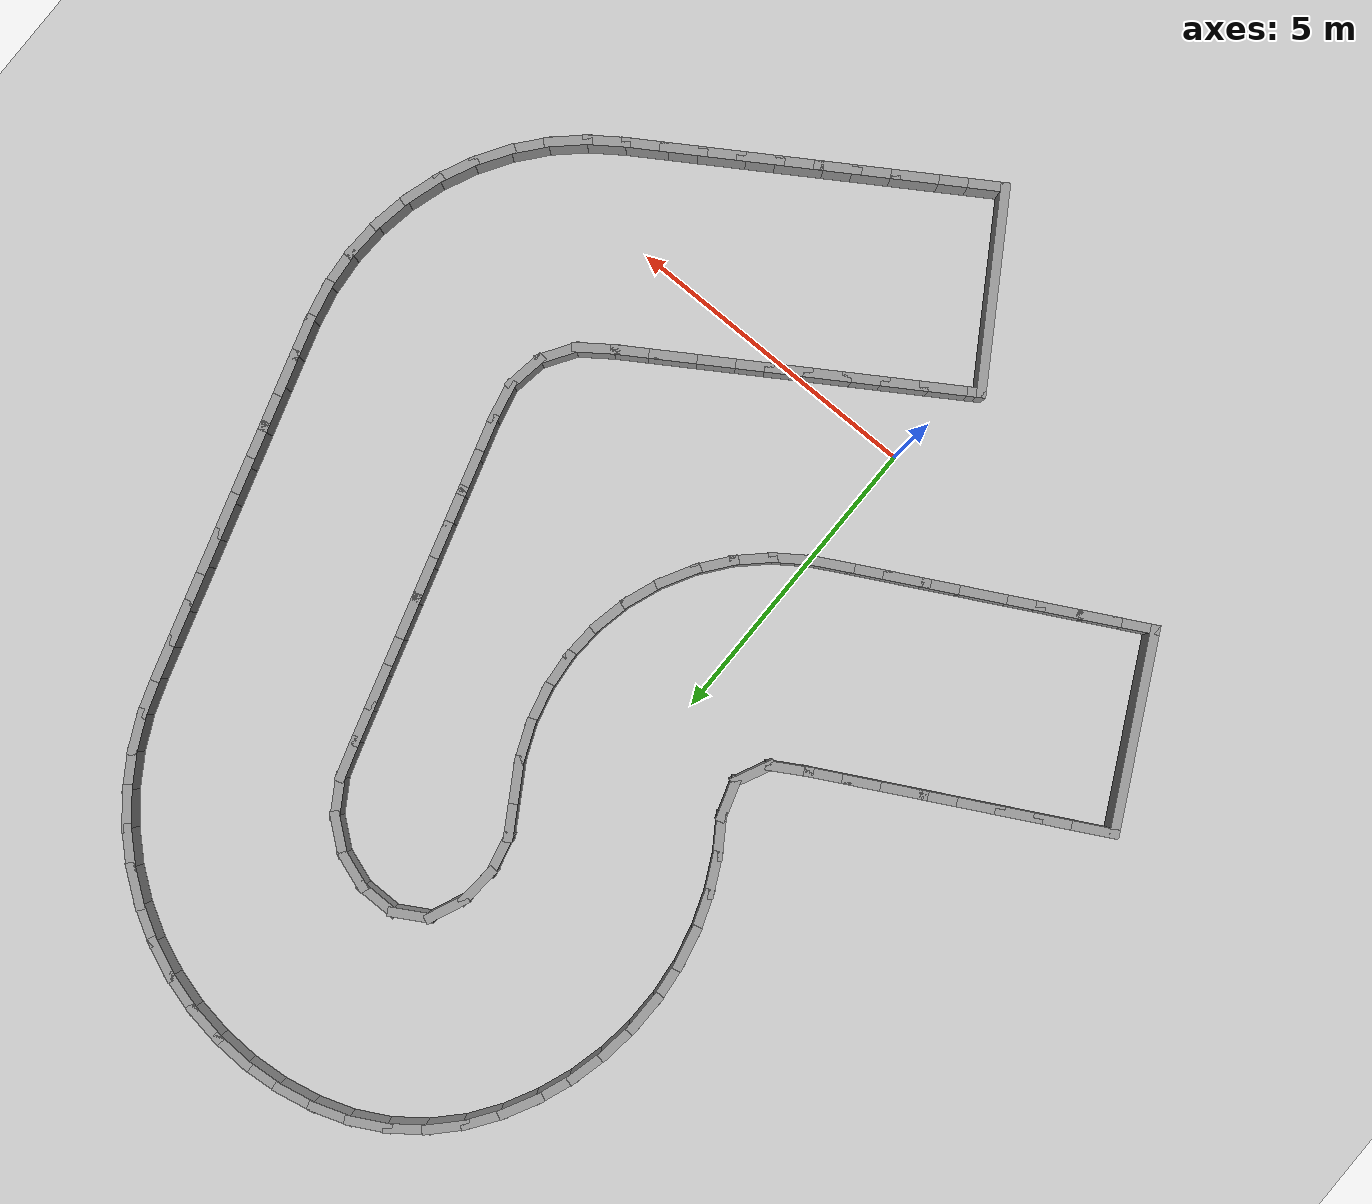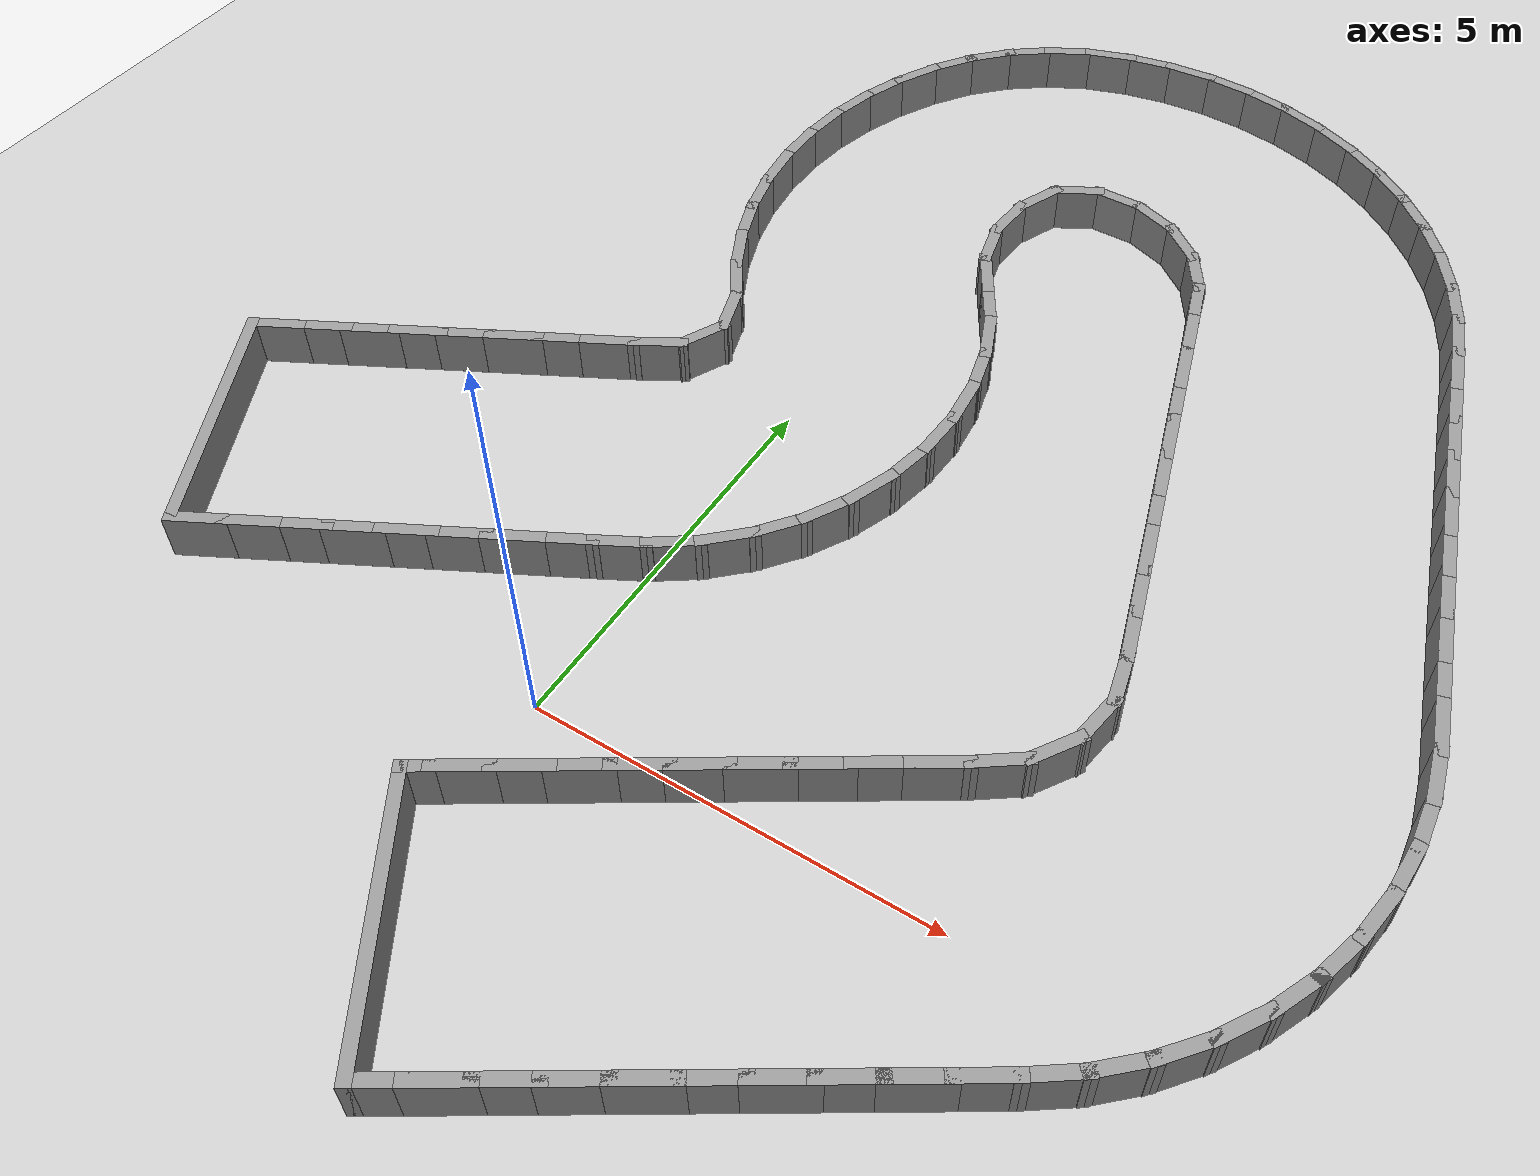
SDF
<?xml version="1.0" ?>
<sdf version='1.7'>
  <world name='default'>
    <plugin name='gazebo_ros_state' filename='libgazebo_ros_state.so'>
      <ros>
        <namespace>/</namespace>
      </ros>
      <update_rate>1000.0</update_rate>
    </plugin>

    <light name='sun' type='directional'>
      <cast_shadows>1</cast_shadows>
      <pose>0 0 10 0 -0 0</pose>
      <diffuse>0.8 0.8 0.8 1</diffuse>
      <specular>0.2 0.2 0.2 1</specular>
      <attenuation>
        <range>1000</range>
        <constant>0.9</constant>
        <linear>0.01</linear>
        <quadratic>0.001</quadratic>
      </attenuation>
      <direction>-0.5 0.1 -0.9</direction>
      <spot>
        <inner_angle>0</inner_angle>
        <outer_angle>0</outer_angle>
        <falloff>0</falloff>
      </spot>
    </light>
    <model name='ground_plane'>
      <static>1</static>
      <link name='link'>
        <collision name='collision'>
          <geometry>
            <plane>
              <normal>0 0 1</normal>
              <size>100 100</size>
            </plane>
          </geometry>
          <surface>
            <friction>
              <ode>
                <mu>100</mu>
                <mu2>50</mu2>
              </ode>
              <torsional>
                <ode/>
              </torsional>
            </friction>
            <contact>
              <ode/>
            </contact>
            <bounce/>
          </surface>
          <max_contacts>10</max_contacts>
        </collision>
        <visual name='visual'>
          <cast_shadows>0</cast_shadows>
          <geometry>
            <plane>
              <normal>0 0 1</normal>
              <size>100 100</size>
            </plane>
          </geometry>
          <material>
            <script>
              <uri>file://media/materials/scripts/gazebo.material</uri>
              <name>Gazebo/Grey</name>
            </script>
          </material>
        </visual>
        <self_collide>0</self_collide>
        <enable_wind>0</enable_wind>
        <kinematic>0</kinematic>
      </link>
    </model>
    <gravity>0 0 -9.8</gravity>
    <magnetic_field>6e-06 2.3e-05 -4.2e-05</magnetic_field>
    <atmosphere type='adiabatic'/>
    <physics type='ode'>
      <max_step_size>0.001</max_step_size>
      <real_time_factor>1</real_time_factor>
      <real_time_update_rate>1000</real_time_update_rate>
    </physics>
    <scene>
      <ambient>0.4 0.4 0.4 1</ambient>
      <background>0.7 0.7 0.7 1</background>
      <shadows>1</shadows>
    </scene>
    <audio>
      <device>default</device>
    </audio>
    <wind/>
    <spherical_coordinates>
      <surface_model>EARTH_WGS84</surface_model>
      <latitude_deg>0</latitude_deg>
      <longitude_deg>0</longitude_deg>
      <elevation>0</elevation>
      <heading_deg>0</heading_deg>
    </spherical_coordinates>
  <model name='rand_turn_04'>
    <pose>0 0 0 0 -0 0</pose>
    <link name='Wall_0'>
      <collision name='Wall_0_Collision'>
        <geometry><box><size>0.7500 0.1500 0.6000</size></box></geometry>
        <pose>0 0 0.3000 0 -0 0</pose>
      </collision>
      <visual name='Wall_0_Visual'>
        <pose>0 0 0.3000 0 -0 0</pose>
        <geometry><box><size>0.7500 0.1500 0.6000</size></box></geometry>
        <material>
          <script>
            <uri>file://media/materials/scripts/gazebo.material</uri>
            <name>Gazebo/Grey</name>
          </script>
          <ambient>1 1 1 1</ambient>
        </material>
      </visual>
      <pose>-6.0179 2.5511 0 0 -0 0.48577</pose>
    </link>
    <link name='Wall_1'>
      <collision name='Wall_1_Collision'>
        <geometry><box><size>0.7500 0.1500 0.6000</size></box></geometry>
        <pose>0 0 0.3000 0 -0 0</pose>
      </collision>
      <visual name='Wall_1_Visual'>
        <pose>0 0 0.3000 0 -0 0</pose>
        <geometry><box><size>0.7500 0.1500 0.6000</size></box></geometry>
        <material>
          <script>
            <uri>file://media/materials/scripts/gazebo.material</uri>
            <name>Gazebo/Grey</name>
          </script>
          <ambient>1 1 1 1</ambient>
        </material>
      </visual>
      <pose>-5.4874 2.8313 0 0 -0 0.48577</pose>
    </link>
    <link name='Wall_2'>
      <collision name='Wall_2_Collision'>
        <geometry><box><size>0.7500 0.1500 0.6000</size></box></geometry>
        <pose>0 0 0.3000 0 -0 0</pose>
      </collision>
      <visual name='Wall_2_Visual'>
        <pose>0 0 0.3000 0 -0 0</pose>
        <geometry><box><size>0.7500 0.1500 0.6000</size></box></geometry>
        <material>
          <script>
            <uri>file://media/materials/scripts/gazebo.material</uri>
            <name>Gazebo/Grey</name>
          </script>
          <ambient>1 1 1 1</ambient>
        </material>
      </visual>
      <pose>-4.9568 3.1114 0 0 -0 0.48577</pose>
    </link>
    <link name='Wall_3'>
      <collision name='Wall_3_Collision'>
        <geometry><box><size>0.7500 0.1500 0.6000</size></box></geometry>
        <pose>0 0 0.3000 0 -0 0</pose>
      </collision>
      <visual name='Wall_3_Visual'>
        <pose>0 0 0.3000 0 -0 0</pose>
        <geometry><box><size>0.7500 0.1500 0.6000</size></box></geometry>
        <material>
          <script>
            <uri>file://media/materials/scripts/gazebo.material</uri>
            <name>Gazebo/Grey</name>
          </script>
          <ambient>1 1 1 1</ambient>
        </material>
      </visual>
      <pose>-4.4262 3.3916 0 0 -0 0.48577</pose>
    </link>
    <link name='Wall_4'>
      <collision name='Wall_4_Collision'>
        <geometry><box><size>0.7500 0.1500 0.6000</size></box></geometry>
        <pose>0 0 0.3000 0 -0 0</pose>
      </collision>
      <visual name='Wall_4_Visual'>
        <pose>0 0 0.3000 0 -0 0</pose>
        <geometry><box><size>0.7500 0.1500 0.6000</size></box></geometry>
        <material>
          <script>
            <uri>file://media/materials/scripts/gazebo.material</uri>
            <name>Gazebo/Grey</name>
          </script>
          <ambient>1 1 1 1</ambient>
        </material>
      </visual>
      <pose>-3.8956 3.6717 0 0 -0 0.48577</pose>
    </link>
    <link name='Wall_5'>
      <collision name='Wall_5_Collision'>
        <geometry><box><size>0.7500 0.1500 0.6000</size></box></geometry>
        <pose>0 0 0.3000 0 -0 0</pose>
      </collision>
      <visual name='Wall_5_Visual'>
        <pose>0 0 0.3000 0 -0 0</pose>
        <geometry><box><size>0.7500 0.1500 0.6000</size></box></geometry>
        <material>
          <script>
            <uri>file://media/materials/scripts/gazebo.material</uri>
            <name>Gazebo/Grey</name>
          </script>
          <ambient>1 1 1 1</ambient>
        </material>
      </visual>
      <pose>-3.3650 3.9518 0 0 -0 0.48577</pose>
    </link>
    <link name='Wall_6'>
      <collision name='Wall_6_Collision'>
        <geometry><box><size>0.7500 0.1500 0.6000</size></box></geometry>
        <pose>0 0 0.3000 0 -0 0</pose>
      </collision>
      <visual name='Wall_6_Visual'>
        <pose>0 0 0.3000 0 -0 0</pose>
        <geometry><box><size>0.7500 0.1500 0.6000</size></box></geometry>
        <material>
          <script>
            <uri>file://media/materials/scripts/gazebo.material</uri>
            <name>Gazebo/Grey</name>
          </script>
          <ambient>1 1 1 1</ambient>
        </material>
      </visual>
      <pose>-2.8344 4.2320 0 0 -0 0.48577</pose>
    </link>
    <link name='Wall_7'>
      <collision name='Wall_7_Collision'>
        <geometry><box><size>0.7500 0.1500 0.6000</size></box></geometry>
        <pose>0 0 0.3000 0 -0 0</pose>
      </collision>
      <visual name='Wall_7_Visual'>
        <pose>0 0 0.3000 0 -0 0</pose>
        <geometry><box><size>0.7500 0.1500 0.6000</size></box></geometry>
        <material>
          <script>
            <uri>file://media/materials/scripts/gazebo.material</uri>
            <name>Gazebo/Grey</name>
          </script>
          <ambient>1 1 1 1</ambient>
        </material>
      </visual>
      <pose>-2.3038 4.5121 0 0 -0 0.48577</pose>
    </link>
    <link name='Wall_8'>
      <collision name='Wall_8_Collision'>
        <geometry><box><size>0.7484 0.1500 0.6000</size></box></geometry>
        <pose>0 0 0.3000 0 -0 0</pose>
      </collision>
      <visual name='Wall_8_Visual'>
        <pose>0 0 0.3000 0 -0 0</pose>
        <geometry><box><size>0.7484 0.1500 0.6000</size></box></geometry>
        <material>
          <script>
            <uri>file://media/materials/scripts/gazebo.material</uri>
            <name>Gazebo/Grey</name>
          </script>
          <ambient>1 1 1 1</ambient>
        </material>
      </visual>
      <pose>-1.7801 4.8029 0 0 -0 0.52795</pose>
    </link>
    <link name='Wall_9'>
      <collision name='Wall_9_Collision'>
        <geometry><box><size>0.7357 0.1500 0.6000</size></box></geometry>
        <pose>0 0 0.3000 0 -0 0</pose>
      </collision>
      <visual name='Wall_9_Visual'>
        <pose>0 0 0.3000 0 -0 0</pose>
        <geometry><box><size>0.7357 0.1500 0.6000</size></box></geometry>
        <material>
          <script>
            <uri>file://media/materials/scripts/gazebo.material</uri>
            <name>Gazebo/Grey</name>
          </script>
          <ambient>1 1 1 1</ambient>
        </material>
      </visual>
      <pose>-1.3938 5.2171 0 0 -0 1.11906</pose>
    </link>
    <link name='Wall_10'>
      <collision name='Wall_10_Collision'>
        <geometry><box><size>0.7359 0.1500 0.6000</size></box></geometry>
        <pose>0 0 0.3000 0 -0 0</pose>
      </collision>
      <visual name='Wall_10_Visual'>
        <pose>0 0 0.3000 0 -0 0</pose>
        <geometry><box><size>0.7359 0.1500 0.6000</size></box></geometry>
        <material>
          <script>
            <uri>file://media/materials/scripts/gazebo.material</uri>
            <name>Gazebo/Grey</name>
          </script>
          <ambient>1 1 1 1</ambient>
        </material>
      </visual>
      <pose>-1.3544 5.7598 0 0 -0 1.87746</pose>
    </link>
    <link name='Wall_11'>
      <collision name='Wall_11_Collision'>
        <geometry><box><size>0.7496 0.1500 0.6000</size></box></geometry>
        <pose>0 0 0.3000 0 -0 0</pose>
      </collision>
      <visual name='Wall_11_Visual'>
        <pose>0 0 0.3000 0 -0 0</pose>
        <geometry><box><size>0.7496 0.1500 0.6000</size></box></geometry>
        <material>
          <script>
            <uri>file://media/materials/scripts/gazebo.material</uri>
            <name>Gazebo/Grey</name>
          </script>
          <ambient>1 1 1 1</ambient>
        </material>
      </visual>
      <pose>-1.6074 6.2897 0 0 -0 2.15180</pose>
    </link>
    <link name='Wall_12'>
      <collision name='Wall_12_Collision'>
        <geometry><box><size>0.7496 0.1500 0.6000</size></box></geometry>
        <pose>0 0 0.3000 0 -0 0</pose>
      </collision>
      <visual name='Wall_12_Visual'>
        <pose>0 0 0.3000 0 -0 0</pose>
        <geometry><box><size>0.7496 0.1500 0.6000</size></box></geometry>
        <material>
          <script>
            <uri>file://media/materials/scripts/gazebo.material</uri>
            <name>Gazebo/Grey</name>
          </script>
          <ambient>1 1 1 1</ambient>
        </material>
      </visual>
      <pose>-1.9059 6.8086 0 0 -0 2.03388</pose>
    </link>
    <link name='Wall_13'>
      <collision name='Wall_13_Collision'>
        <geometry><box><size>0.7497 0.1500 0.6000</size></box></geometry>
        <pose>0 0 0.3000 0 -0 0</pose>
      </collision>
      <visual name='Wall_13_Visual'>
        <pose>0 0 0.3000 0 -0 0</pose>
        <geometry><box><size>0.7497 0.1500 0.6000</size></box></geometry>
        <material>
          <script>
            <uri>file://media/materials/scripts/gazebo.material</uri>
            <name>Gazebo/Grey</name>
          </script>
          <ambient>1 1 1 1</ambient>
        </material>
      </visual>
      <pose>-2.1413 7.3589 0 0 -0 1.91606</pose>
    </link>
    <link name='Wall_14'>
      <collision name='Wall_14_Collision'>
        <geometry><box><size>0.7497 0.1500 0.6000</size></box></geometry>
        <pose>0 0 0.3000 0 -0 0</pose>
      </collision>
      <visual name='Wall_14_Visual'>
        <pose>0 0 0.3000 0 -0 0</pose>
        <geometry><box><size>0.7497 0.1500 0.6000</size></box></geometry>
        <material>
          <script>
            <uri>file://media/materials/scripts/gazebo.material</uri>
            <name>Gazebo/Grey</name>
          </script>
          <ambient>1 1 1 1</ambient>
        </material>
      </visual>
      <pose>-2.3101 7.9332 0 0 -0 1.79754</pose>
    </link>
    <link name='Wall_15'>
      <collision name='Wall_15_Collision'>
        <geometry><box><size>0.7496 0.1500 0.6000</size></box></geometry>
        <pose>0 0 0.3000 0 -0 0</pose>
      </collision>
      <visual name='Wall_15_Visual'>
        <pose>0 0 0.3000 0 -0 0</pose>
        <geometry><box><size>0.7496 0.1500 0.6000</size></box></geometry>
        <material>
          <script>
            <uri>file://media/materials/scripts/gazebo.material</uri>
            <name>Gazebo/Grey</name>
          </script>
          <ambient>1 1 1 1</ambient>
        </material>
      </visual>
      <pose>-2.4101 8.5234 0 0 -0 1.67965</pose>
    </link>
    <link name='Wall_16'>
      <collision name='Wall_16_Collision'>
        <geometry><box><size>0.7496 0.1500 0.6000</size></box></geometry>
        <pose>0 0 0.3000 0 -0 0</pose>
      </collision>
      <visual name='Wall_16_Visual'>
        <pose>0 0 0.3000 0 -0 0</pose>
        <geometry><box><size>0.7496 0.1500 0.6000</size></box></geometry>
        <material>
          <script>
            <uri>file://media/materials/scripts/gazebo.material</uri>
            <name>Gazebo/Grey</name>
          </script>
          <ambient>1 1 1 1</ambient>
        </material>
      </visual>
      <pose>-2.4400 9.1213 0 0 -0 1.56183</pose>
    </link>
    <link name='Wall_17'>
      <collision name='Wall_17_Collision'>
        <geometry><box><size>0.7496 0.1500 0.6000</size></box></geometry>
        <pose>0 0 0.3000 0 -0 0</pose>
      </collision>
      <visual name='Wall_17_Visual'>
        <pose>0 0 0.3000 0 -0 0</pose>
        <geometry><box><size>0.7496 0.1500 0.6000</size></box></geometry>
        <material>
          <script>
            <uri>file://media/materials/scripts/gazebo.material</uri>
            <name>Gazebo/Grey</name>
          </script>
          <ambient>1 1 1 1</ambient>
        </material>
      </visual>
      <pose>-2.3994 9.7185 0 0 -0 1.44400</pose>
    </link>
    <link name='Wall_18'>
      <collision name='Wall_18_Collision'>
        <geometry><box><size>0.7496 0.1500 0.6000</size></box></geometry>
        <pose>0 0 0.3000 0 -0 0</pose>
      </collision>
      <visual name='Wall_18_Visual'>
        <pose>0 0 0.3000 0 -0 0</pose>
        <geometry><box><size>0.7496 0.1500 0.6000</size></box></geometry>
        <material>
          <script>
            <uri>file://media/materials/scripts/gazebo.material</uri>
            <name>Gazebo/Grey</name>
          </script>
          <ambient>1 1 1 1</ambient>
        </material>
      </visual>
      <pose>-2.2889 10.3068 0 0 -0 1.32618</pose>
    </link>
    <link name='Wall_19'>
      <collision name='Wall_19_Collision'>
        <geometry><box><size>0.7496 0.1500 0.6000</size></box></geometry>
        <pose>0 0 0.3000 0 -0 0</pose>
      </collision>
      <visual name='Wall_19_Visual'>
        <pose>0 0 0.3000 0 -0 0</pose>
        <geometry><box><size>0.7496 0.1500 0.6000</size></box></geometry>
        <material>
          <script>
            <uri>file://media/materials/scripts/gazebo.material</uri>
            <name>Gazebo/Grey</name>
          </script>
          <ambient>1 1 1 1</ambient>
        </material>
      </visual>
      <pose>-2.1100 10.8780 0 0 -0 1.20836</pose>
    </link>
    <link name='Wall_20'>
      <collision name='Wall_20_Collision'>
        <geometry><box><size>0.7496 0.1500 0.6000</size></box></geometry>
        <pose>0 0 0.3000 0 -0 0</pose>
      </collision>
      <visual name='Wall_20_Visual'>
        <pose>0 0 0.3000 0 -0 0</pose>
        <geometry><box><size>0.7496 0.1500 0.6000</size></box></geometry>
        <material>
          <script>
            <uri>file://media/materials/scripts/gazebo.material</uri>
            <name>Gazebo/Grey</name>
          </script>
          <ambient>1 1 1 1</ambient>
        </material>
      </visual>
      <pose>-1.8652 11.4242 0 0 -0 1.09053</pose>
    </link>
    <link name='Wall_21'>
      <collision name='Wall_21_Collision'>
        <geometry><box><size>0.7494 0.1500 0.6000</size></box></geometry>
        <pose>0 0 0.3000 0 -0 0</pose>
      </collision>
      <visual name='Wall_21_Visual'>
        <pose>0 0 0.3000 0 -0 0</pose>
        <geometry><box><size>0.7494 0.1500 0.6000</size></box></geometry>
        <material>
          <script>
            <uri>file://media/materials/scripts/gazebo.material</uri>
            <name>Gazebo/Grey</name>
          </script>
          <ambient>1 1 1 1</ambient>
        </material>
      </visual>
      <pose>-1.5556 11.9361 0 0 -0 0.96325</pose>
    </link>
    <link name='Wall_22'>
      <collision name='Wall_22_Collision'>
        <geometry><box><size>0.7493 0.1500 0.6000</size></box></geometry>
        <pose>0 0 0.3000 0 -0 0</pose>
      </collision>
      <visual name='Wall_22_Visual'>
        <pose>0 0 0.3000 0 -0 0</pose>
        <geometry><box><size>0.7493 0.1500 0.6000</size></box></geometry>
        <material>
          <script>
            <uri>file://media/materials/scripts/gazebo.material</uri>
            <name>Gazebo/Grey</name>
          </script>
          <ambient>1 1 1 1</ambient>
        </material>
      </visual>
      <pose>-1.1772 12.3986 0 0 -0 0.80688</pose>
    </link>
    <link name='Wall_23'>
      <collision name='Wall_23_Collision'>
        <geometry><box><size>0.7493 0.1500 0.6000</size></box></geometry>
        <pose>0 0 0.3000 0 -0 0</pose>
      </collision>
      <visual name='Wall_23_Visual'>
        <pose>0 0 0.3000 0 -0 0</pose>
        <geometry><box><size>0.7493 0.1500 0.6000</size></box></geometry>
        <material>
          <script>
            <uri>file://media/materials/scripts/gazebo.material</uri>
            <name>Gazebo/Grey</name>
          </script>
          <ambient>1 1 1 1</ambient>
        </material>
      </visual>
      <pose>-0.7307 12.7955 0 0 -0 0.64634</pose>
    </link>
    <link name='Wall_24'>
      <collision name='Wall_24_Collision'>
        <geometry><box><size>0.7493 0.1500 0.6000</size></box></geometry>
        <pose>0 0 0.3000 0 -0 0</pose>
      </collision>
      <visual name='Wall_24_Visual'>
        <pose>0 0 0.3000 0 -0 0</pose>
        <geometry><box><size>0.7493 0.1500 0.6000</size></box></geometry>
        <material>
          <script>
            <uri>file://media/materials/scripts/gazebo.material</uri>
            <name>Gazebo/Grey</name>
          </script>
          <ambient>1 1 1 1</ambient>
        </material>
      </visual>
      <pose>-0.2268 13.1165 0 0 -0 0.48820</pose>
    </link>
    <link name='Wall_25'>
      <collision name='Wall_25_Collision'>
        <geometry><box><size>0.7493 0.1500 0.6000</size></box></geometry>
        <pose>0 0 0.3000 0 -0 0</pose>
      </collision>
      <visual name='Wall_25_Visual'>
        <pose>0 0 0.3000 0 -0 0</pose>
        <geometry><box><size>0.7493 0.1500 0.6000</size></box></geometry>
        <material>
          <script>
            <uri>file://media/materials/scripts/gazebo.material</uri>
            <name>Gazebo/Grey</name>
          </script>
          <ambient>1 1 1 1</ambient>
        </material>
      </visual>
      <pose>0.3219 13.3523 0 0 -0 0.32374</pose>
    </link>
    <link name='Wall_26'>
      <collision name='Wall_26_Collision'>
        <geometry><box><size>0.7496 0.1500 0.6000</size></box></geometry>
        <pose>0 0 0.3000 0 -0 0</pose>
      </collision>
      <visual name='Wall_26_Visual'>
        <pose>0 0 0.3000 0 -0 0</pose>
        <geometry><box><size>0.7496 0.1500 0.6000</size></box></geometry>
        <material>
          <script>
            <uri>file://media/materials/scripts/gazebo.material</uri>
            <name>Gazebo/Grey</name>
          </script>
          <ambient>1 1 1 1</ambient>
        </material>
      </visual>
      <pose>0.9003 13.5045 0 0 -0 0.19081</pose>
    </link>
    <link name='Wall_27'>
      <collision name='Wall_27_Collision'>
        <geometry><box><size>0.7496 0.1500 0.6000</size></box></geometry>
        <pose>0 0 0.3000 0 -0 0</pose>
      </collision>
      <visual name='Wall_27_Visual'>
        <pose>0 0 0.3000 0 -0 0</pose>
        <geometry><box><size>0.7496 0.1500 0.6000</size></box></geometry>
        <material>
          <script>
            <uri>file://media/materials/scripts/gazebo.material</uri>
            <name>Gazebo/Grey</name>
          </script>
          <ambient>1 1 1 1</ambient>
        </material>
      </visual>
      <pose>1.4937 13.5824 0 0 -0 0.07019</pose>
    </link>
    <link name='Wall_28'>
      <collision name='Wall_28_Collision'>
        <geometry><box><size>0.7496 0.1500 0.6000</size></box></geometry>
        <pose>0 0 0.3000 0 -0 0</pose>
      </collision>
      <visual name='Wall_28_Visual'>
        <pose>0 0 0.3000 0 -0 0</pose>
        <geometry><box><size>0.7496 0.1500 0.6000</size></box></geometry>
        <material>
          <script>
            <uri>file://media/materials/scripts/gazebo.material</uri>
            <name>Gazebo/Grey</name>
          </script>
          <ambient>1 1 1 1</ambient>
        </material>
      </visual>
      <pose>2.0922 13.5883 0 0 -0 -0.05044</pose>
    </link>
    <link name='Wall_29'>
      <collision name='Wall_29_Collision'>
        <geometry><box><size>0.7496 0.1500 0.6000</size></box></geometry>
        <pose>0 0 0.3000 0 -0 0</pose>
      </collision>
      <visual name='Wall_29_Visual'>
        <pose>0 0 0.3000 0 -0 0</pose>
        <geometry><box><size>0.7496 0.1500 0.6000</size></box></geometry>
        <material>
          <script>
            <uri>file://media/materials/scripts/gazebo.material</uri>
            <name>Gazebo/Grey</name>
          </script>
          <ambient>1 1 1 1</ambient>
        </material>
      </visual>
      <pose>2.6870 13.5222 0 0 -0 -0.17106</pose>
    </link>
    <link name='Wall_30'>
      <collision name='Wall_30_Collision'>
        <geometry><box><size>0.7496 0.1500 0.6000</size></box></geometry>
        <pose>0 0 0.3000 0 -0 0</pose>
      </collision>
      <visual name='Wall_30_Visual'>
        <pose>0 0 0.3000 0 -0 0</pose>
        <geometry><box><size>0.7496 0.1500 0.6000</size></box></geometry>
        <material>
          <script>
            <uri>file://media/materials/scripts/gazebo.material</uri>
            <name>Gazebo/Grey</name>
          </script>
          <ambient>1 1 1 1</ambient>
        </material>
      </visual>
      <pose>3.2696 13.3849 0 0 -0 -0.29168</pose>
    </link>
    <link name='Wall_31'>
      <collision name='Wall_31_Collision'>
        <geometry><box><size>0.7496 0.1500 0.6000</size></box></geometry>
        <pose>0 0 0.3000 0 -0 0</pose>
      </collision>
      <visual name='Wall_31_Visual'>
        <pose>0 0 0.3000 0 -0 0</pose>
        <geometry><box><size>0.7496 0.1500 0.6000</size></box></geometry>
        <material>
          <script>
            <uri>file://media/materials/scripts/gazebo.material</uri>
            <name>Gazebo/Grey</name>
          </script>
          <ambient>1 1 1 1</ambient>
        </material>
      </visual>
      <pose>3.8314 13.1786 0 0 -0 -0.41231</pose>
    </link>
    <link name='Wall_32'>
      <collision name='Wall_32_Collision'>
        <geometry><box><size>0.7496 0.1500 0.6000</size></box></geometry>
        <pose>0 0 0.3000 0 -0 0</pose>
      </collision>
      <visual name='Wall_32_Visual'>
        <pose>0 0 0.3000 0 -0 0</pose>
        <geometry><box><size>0.7496 0.1500 0.6000</size></box></geometry>
        <material>
          <script>
            <uri>file://media/materials/scripts/gazebo.material</uri>
            <name>Gazebo/Grey</name>
          </script>
          <ambient>1 1 1 1</ambient>
        </material>
      </visual>
      <pose>4.3643 12.9061 0 0 -0 -0.53293</pose>
    </link>
    <link name='Wall_33'>
      <collision name='Wall_33_Collision'>
        <geometry><box><size>0.7496 0.1500 0.6000</size></box></geometry>
        <pose>0 0 0.3000 0 -0 0</pose>
      </collision>
      <visual name='Wall_33_Visual'>
        <pose>0 0 0.3000 0 -0 0</pose>
        <geometry><box><size>0.7496 0.1500 0.6000</size></box></geometry>
        <material>
          <script>
            <uri>file://media/materials/scripts/gazebo.material</uri>
            <name>Gazebo/Grey</name>
          </script>
          <ambient>1 1 1 1</ambient>
        </material>
      </visual>
      <pose>4.8605 12.5715 0 0 -0 -0.65356</pose>
    </link>
    <link name='Wall_34'>
      <collision name='Wall_34_Collision'>
        <geometry><box><size>0.7496 0.1500 0.6000</size></box></geometry>
        <pose>0 0 0.3000 0 -0 0</pose>
      </collision>
      <visual name='Wall_34_Visual'>
        <pose>0 0 0.3000 0 -0 0</pose>
        <geometry><box><size>0.7496 0.1500 0.6000</size></box></geometry>
        <material>
          <script>
            <uri>file://media/materials/scripts/gazebo.material</uri>
            <name>Gazebo/Grey</name>
          </script>
          <ambient>1 1 1 1</ambient>
        </material>
      </visual>
      <pose>5.3129 12.1796 0 0 -0 -0.77418</pose>
    </link>
    <link name='Wall_35'>
      <collision name='Wall_35_Collision'>
        <geometry><box><size>0.7496 0.1500 0.6000</size></box></geometry>
        <pose>0 0 0.3000 0 -0 0</pose>
      </collision>
      <visual name='Wall_35_Visual'>
        <pose>0 0 0.3000 0 -0 0</pose>
        <geometry><box><size>0.7496 0.1500 0.6000</size></box></geometry>
        <material>
          <script>
            <uri>file://media/materials/scripts/gazebo.material</uri>
            <name>Gazebo/Grey</name>
          </script>
          <ambient>1 1 1 1</ambient>
        </material>
      </visual>
      <pose>5.7149 11.7361 0 0 -0 -0.89480</pose>
    </link>
    <link name='Wall_36'>
      <collision name='Wall_36_Collision'>
        <geometry><box><size>0.7496 0.1500 0.6000</size></box></geometry>
        <pose>0 0 0.3000 0 -0 0</pose>
      </collision>
      <visual name='Wall_36_Visual'>
        <pose>0 0 0.3000 0 -0 0</pose>
        <geometry><box><size>0.7496 0.1500 0.6000</size></box></geometry>
        <material>
          <script>
            <uri>file://media/materials/scripts/gazebo.material</uri>
            <name>Gazebo/Grey</name>
          </script>
          <ambient>1 1 1 1</ambient>
        </material>
      </visual>
      <pose>6.0605 11.2475 0 0 -0 -1.01543</pose>
    </link>
    <link name='Wall_37'>
      <collision name='Wall_37_Collision'>
        <geometry><box><size>0.7496 0.1500 0.6000</size></box></geometry>
        <pose>0 0 0.3000 0 -0 0</pose>
      </collision>
      <visual name='Wall_37_Visual'>
        <pose>0 0 0.3000 0 -0 0</pose>
        <geometry><box><size>0.7496 0.1500 0.6000</size></box></geometry>
        <material>
          <script>
            <uri>file://media/materials/scripts/gazebo.material</uri>
            <name>Gazebo/Grey</name>
          </script>
          <ambient>1 1 1 1</ambient>
        </material>
      </visual>
      <pose>6.3448 10.7208 0 0 -0 -1.13624</pose>
    </link>
    <link name='Wall_38'>
      <collision name='Wall_38_Collision'>
        <geometry><box><size>0.7497 0.1500 0.6000</size></box></geometry>
        <pose>0 0 0.3000 0 -0 0</pose>
      </collision>
      <visual name='Wall_38_Visual'>
        <pose>0 0 0.3000 0 -0 0</pose>
        <geometry><box><size>0.7497 0.1500 0.6000</size></box></geometry>
        <material>
          <script>
            <uri>file://media/materials/scripts/gazebo.material</uri>
            <name>Gazebo/Grey</name>
          </script>
          <ambient>1 1 1 1</ambient>
        </material>
      </visual>
      <pose>6.5647 10.1640 0 0 -0 -1.25315</pose>
    </link>
    <link name='Wall_39'>
      <collision name='Wall_39_Collision'>
        <geometry><box><size>0.7500 0.1500 0.6000</size></box></geometry>
        <pose>0 0 0.3000 0 -0 0</pose>
      </collision>
      <visual name='Wall_39_Visual'>
        <pose>0 0 0.3000 0 -0 0</pose>
        <geometry><box><size>0.7500 0.1500 0.6000</size></box></geometry>
        <material>
          <script>
            <uri>file://media/materials/scripts/gazebo.material</uri>
            <name>Gazebo/Grey</name>
          </script>
          <ambient>1 1 1 1</ambient>
        </material>
      </visual>
      <pose>6.7423 9.5911 0 0 -0 -1.28732</pose>
    </link>
    <link name='Wall_40'>
      <collision name='Wall_40_Collision'>
        <geometry><box><size>0.7500 0.1500 0.6000</size></box></geometry>
        <pose>0 0 0.3000 0 -0 0</pose>
      </collision>
      <visual name='Wall_40_Visual'>
        <pose>0 0 0.3000 0 -0 0</pose>
        <geometry><box><size>0.7500 0.1500 0.6000</size></box></geometry>
        <material>
          <script>
            <uri>file://media/materials/scripts/gazebo.material</uri>
            <name>Gazebo/Grey</name>
          </script>
          <ambient>1 1 1 1</ambient>
        </material>
      </visual>
      <pose>6.9101 9.0150 0 0 -0 -1.28732</pose>
    </link>
    <link name='Wall_41'>
      <collision name='Wall_41_Collision'>
        <geometry><box><size>0.7500 0.1500 0.6000</size></box></geometry>
        <pose>0 0 0.3000 0 -0 0</pose>
      </collision>
      <visual name='Wall_41_Visual'>
        <pose>0 0 0.3000 0 -0 0</pose>
        <geometry><box><size>0.7500 0.1500 0.6000</size></box></geometry>
        <material>
          <script>
            <uri>file://media/materials/scripts/gazebo.material</uri>
            <name>Gazebo/Grey</name>
          </script>
          <ambient>1 1 1 1</ambient>
        </material>
      </visual>
      <pose>7.0779 8.4390 0 0 -0 -1.28732</pose>
    </link>
    <link name='Wall_42'>
      <collision name='Wall_42_Collision'>
        <geometry><box><size>0.7500 0.1500 0.6000</size></box></geometry>
        <pose>0 0 0.3000 0 -0 0</pose>
      </collision>
      <visual name='Wall_42_Visual'>
        <pose>0 0 0.3000 0 -0 0</pose>
        <geometry><box><size>0.7500 0.1500 0.6000</size></box></geometry>
        <material>
          <script>
            <uri>file://media/materials/scripts/gazebo.material</uri>
            <name>Gazebo/Grey</name>
          </script>
          <ambient>1 1 1 1</ambient>
        </material>
      </visual>
      <pose>7.2458 7.8629 0 0 -0 -1.28732</pose>
    </link>
    <link name='Wall_43'>
      <collision name='Wall_43_Collision'>
        <geometry><box><size>0.7500 0.1500 0.6000</size></box></geometry>
        <pose>0 0 0.3000 0 -0 0</pose>
      </collision>
      <visual name='Wall_43_Visual'>
        <pose>0 0 0.3000 0 -0 0</pose>
        <geometry><box><size>0.7500 0.1500 0.6000</size></box></geometry>
        <material>
          <script>
            <uri>file://media/materials/scripts/gazebo.material</uri>
            <name>Gazebo/Grey</name>
          </script>
          <ambient>1 1 1 1</ambient>
        </material>
      </visual>
      <pose>7.4136 7.2869 0 0 -0 -1.28732</pose>
    </link>
    <link name='Wall_44'>
      <collision name='Wall_44_Collision'>
        <geometry><box><size>0.7500 0.1500 0.6000</size></box></geometry>
        <pose>0 0 0.3000 0 -0 0</pose>
      </collision>
      <visual name='Wall_44_Visual'>
        <pose>0 0 0.3000 0 -0 0</pose>
        <geometry><box><size>0.7500 0.1500 0.6000</size></box></geometry>
        <material>
          <script>
            <uri>file://media/materials/scripts/gazebo.material</uri>
            <name>Gazebo/Grey</name>
          </script>
          <ambient>1 1 1 1</ambient>
        </material>
      </visual>
      <pose>7.5814 6.7108 0 0 -0 -1.28732</pose>
    </link>
    <link name='Wall_45'>
      <collision name='Wall_45_Collision'>
        <geometry><box><size>0.7500 0.1500 0.6000</size></box></geometry>
        <pose>0 0 0.3000 0 -0 0</pose>
      </collision>
      <visual name='Wall_45_Visual'>
        <pose>0 0 0.3000 0 -0 0</pose>
        <geometry><box><size>0.7500 0.1500 0.6000</size></box></geometry>
        <material>
          <script>
            <uri>file://media/materials/scripts/gazebo.material</uri>
            <name>Gazebo/Grey</name>
          </script>
          <ambient>1 1 1 1</ambient>
        </material>
      </visual>
      <pose>7.7492 6.1348 0 0 -0 -1.28732</pose>
    </link>
    <link name='Wall_46'>
      <collision name='Wall_46_Collision'>
        <geometry><box><size>0.7500 0.1500 0.6000</size></box></geometry>
        <pose>0 0 0.3000 0 -0 0</pose>
      </collision>
      <visual name='Wall_46_Visual'>
        <pose>0 0 0.3000 0 -0 0</pose>
        <geometry><box><size>0.7500 0.1500 0.6000</size></box></geometry>
        <material>
          <script>
            <uri>file://media/materials/scripts/gazebo.material</uri>
            <name>Gazebo/Grey</name>
          </script>
          <ambient>1 1 1 1</ambient>
        </material>
      </visual>
      <pose>7.9170 5.5587 0 0 -0 -1.28732</pose>
    </link>
    <link name='Wall_47'>
      <collision name='Wall_47_Collision'>
        <geometry><box><size>0.7500 0.1500 0.6000</size></box></geometry>
        <pose>0 0 0.3000 0 -0 0</pose>
      </collision>
      <visual name='Wall_47_Visual'>
        <pose>0 0 0.3000 0 -0 0</pose>
        <geometry><box><size>0.7500 0.1500 0.6000</size></box></geometry>
        <material>
          <script>
            <uri>file://media/materials/scripts/gazebo.material</uri>
            <name>Gazebo/Grey</name>
          </script>
          <ambient>1 1 1 1</ambient>
        </material>
      </visual>
      <pose>8.0849 4.9826 0 0 -0 -1.28732</pose>
    </link>
    <link name='Wall_48'>
      <collision name='Wall_48_Collision'>
        <geometry><box><size>0.7500 0.1500 0.6000</size></box></geometry>
        <pose>0 0 0.3000 0 -0 0</pose>
      </collision>
      <visual name='Wall_48_Visual'>
        <pose>0 0 0.3000 0 -0 0</pose>
        <geometry><box><size>0.7500 0.1500 0.6000</size></box></geometry>
        <material>
          <script>
            <uri>file://media/materials/scripts/gazebo.material</uri>
            <name>Gazebo/Grey</name>
          </script>
          <ambient>1 1 1 1</ambient>
        </material>
      </visual>
      <pose>8.2523 4.4065 0 0 -0 -1.28869</pose>
    </link>
    <link name='Wall_49'>
      <collision name='Wall_49_Collision'>
        <geometry><box><size>0.7495 0.1500 0.6000</size></box></geometry>
        <pose>0 0 0.3000 0 -0 0</pose>
      </collision>
      <visual name='Wall_49_Visual'>
        <pose>0 0 0.3000 0 -0 0</pose>
        <geometry><box><size>0.7495 0.1500 0.6000</size></box></geometry>
        <material>
          <script>
            <uri>file://media/materials/scripts/gazebo.material</uri>
            <name>Gazebo/Grey</name>
          </script>
          <ambient>1 1 1 1</ambient>
        </material>
      </visual>
      <pose>8.3973 3.8250 0 0 -0 -1.36404</pose>
    </link>
    <link name='Wall_50'>
      <collision name='Wall_50_Collision'>
        <geometry><box><size>0.7495 0.1500 0.6000</size></box></geometry>
        <pose>0 0 0.3000 0 -0 0</pose>
      </collision>
      <visual name='Wall_50_Visual'>
        <pose>0 0 0.3000 0 -0 0</pose>
        <geometry><box><size>0.7495 0.1500 0.6000</size></box></geometry>
        <material>
          <script>
            <uri>file://media/materials/scripts/gazebo.material</uri>
            <name>Gazebo/Grey</name>
          </script>
          <ambient>1 1 1 1</ambient>
        </material>
      </visual>
      <pose>8.4823 3.2327 0 0 -0 -1.49255</pose>
    </link>
    <link name='Wall_51'>
      <collision name='Wall_51_Collision'>
        <geometry><box><size>0.7496 0.1500 0.6000</size></box></geometry>
        <pose>0 0 0.3000 0 -0 0</pose>
      </collision>
      <visual name='Wall_51_Visual'>
        <pose>0 0 0.3000 0 -0 0</pose>
        <geometry><box><size>0.7496 0.1500 0.6000</size></box></geometry>
        <material>
          <script>
            <uri>file://media/materials/scripts/gazebo.material</uri>
            <name>Gazebo/Grey</name>
          </script>
          <ambient>1 1 1 1</ambient>
        </material>
      </visual>
      <pose>8.4906 2.6345 0 0 -0 -1.62125</pose>
    </link>
    <link name='Wall_52'>
      <collision name='Wall_52_Collision'>
        <geometry><box><size>0.7496 0.1500 0.6000</size></box></geometry>
        <pose>0 0 0.3000 0 -0 0</pose>
      </collision>
      <visual name='Wall_52_Visual'>
        <pose>0 0 0.3000 0 -0 0</pose>
        <geometry><box><size>0.7496 0.1500 0.6000</size></box></geometry>
        <material>
          <script>
            <uri>file://media/materials/scripts/gazebo.material</uri>
            <name>Gazebo/Grey</name>
          </script>
          <ambient>1 1 1 1</ambient>
        </material>
      </visual>
      <pose>8.4221 2.0401 0 0 -0 -1.74994</pose>
    </link>
    <link name='Wall_53'>
      <collision name='Wall_53_Collision'>
        <geometry><box><size>0.7496 0.1500 0.6000</size></box></geometry>
        <pose>0 0 0.3000 0 -0 0</pose>
      </collision>
      <visual name='Wall_53_Visual'>
        <pose>0 0 0.3000 0 -0 0</pose>
        <geometry><box><size>0.7496 0.1500 0.6000</size></box></geometry>
        <material>
          <script>
            <uri>file://media/materials/scripts/gazebo.material</uri>
            <name>Gazebo/Grey</name>
          </script>
          <ambient>1 1 1 1</ambient>
        </material>
      </visual>
      <pose>8.2778 1.4594 0 0 -0 -1.87863</pose>
    </link>
    <link name='Wall_54'>
      <collision name='Wall_54_Collision'>
        <geometry><box><size>0.7496 0.1500 0.6000</size></box></geometry>
        <pose>0 0 0.3000 0 -0 0</pose>
      </collision>
      <visual name='Wall_54_Visual'>
        <pose>0 0 0.3000 0 -0 0</pose>
        <geometry><box><size>0.7496 0.1500 0.6000</size></box></geometry>
        <material>
          <script>
            <uri>file://media/materials/scripts/gazebo.material</uri>
            <name>Gazebo/Grey</name>
          </script>
          <ambient>1 1 1 1</ambient>
        </material>
      </visual>
      <pose>8.0602 0.9020 0 0 -0 -2.00741</pose>
    </link>
    <link name='Wall_55'>
      <collision name='Wall_55_Collision'>
        <geometry><box><size>0.7496 0.1500 0.6000</size></box></geometry>
        <pose>0 0 0.3000 0 -0 0</pose>
      </collision>
      <visual name='Wall_55_Visual'>
        <pose>0 0 0.3000 0 -0 0</pose>
        <geometry><box><size>0.7496 0.1500 0.6000</size></box></geometry>
        <material>
          <script>
            <uri>file://media/materials/scripts/gazebo.material</uri>
            <name>Gazebo/Grey</name>
          </script>
          <ambient>1 1 1 1</ambient>
        </material>
      </visual>
      <pose>7.7727 0.3772 0 0 -0 -2.13655</pose>
    </link>
    <link name='Wall_56'>
      <collision name='Wall_56_Collision'>
        <geometry><box><size>0.7496 0.1500 0.6000</size></box></geometry>
        <pose>0 0 0.3000 0 -0 0</pose>
      </collision>
      <visual name='Wall_56_Visual'>
        <pose>0 0 0.3000 0 -0 0</pose>
        <geometry><box><size>0.7496 0.1500 0.6000</size></box></geometry>
        <material>
          <script>
            <uri>file://media/materials/scripts/gazebo.material</uri>
            <name>Gazebo/Grey</name>
          </script>
          <ambient>1 1 1 1</ambient>
        </material>
      </visual>
      <pose>7.4202 -0.1062 0 0 -0 -2.26525</pose>
    </link>
    <link name='Wall_57'>
      <collision name='Wall_57_Collision'>
        <geometry><box><size>0.7496 0.1500 0.6000</size></box></geometry>
        <pose>0 0 0.3000 0 -0 0</pose>
      </collision>
      <visual name='Wall_57_Visual'>
        <pose>0 0 0.3000 0 -0 0</pose>
        <geometry><box><size>0.7496 0.1500 0.6000</size></box></geometry>
        <material>
          <script>
            <uri>file://media/materials/scripts/gazebo.material</uri>
            <name>Gazebo/Grey</name>
          </script>
          <ambient>1 1 1 1</ambient>
        </material>
      </visual>
      <pose>7.0085 -0.5404 0 0 -0 -2.39394</pose>
    </link>
    <link name='Wall_58'>
      <collision name='Wall_58_Collision'>
        <geometry><box><size>0.7496 0.1500 0.6000</size></box></geometry>
        <pose>0 0 0.3000 0 -0 0</pose>
      </collision>
      <visual name='Wall_58_Visual'>
        <pose>0 0 0.3000 0 -0 0</pose>
        <geometry><box><size>0.7496 0.1500 0.6000</size></box></geometry>
        <material>
          <script>
            <uri>file://media/materials/scripts/gazebo.material</uri>
            <name>Gazebo/Grey</name>
          </script>
          <ambient>1 1 1 1</ambient>
        </material>
      </visual>
      <pose>6.5446 -0.9184 0 0 -0 -2.52158</pose>
    </link>
    <link name='Wall_59'>
      <collision name='Wall_59_Collision'>
        <geometry><box><size>0.7500 0.1500 0.6000</size></box></geometry>
        <pose>0 0 0.3000 0 -0 0</pose>
      </collision>
      <visual name='Wall_59_Visual'>
        <pose>0 0 0.3000 0 -0 0</pose>
        <geometry><box><size>0.7500 0.1500 0.6000</size></box></geometry>
        <material>
          <script>
            <uri>file://media/materials/scripts/gazebo.material</uri>
            <name>Gazebo/Grey</name>
          </script>
          <ambient>1 1 1 1</ambient>
        </material>
      </visual>
      <pose>6.0476 -1.2538 0 0 -0 -2.57446</pose>
    </link>
    <link name='Wall_60'>
      <collision name='Wall_60_Collision'>
        <geometry><box><size>0.7500 0.1500 0.6000</size></box></geometry>
        <pose>0 0 0.3000 0 -0 0</pose>
      </collision>
      <visual name='Wall_60_Visual'>
        <pose>0 0 0.3000 0 -0 0</pose>
        <geometry><box><size>0.7500 0.1500 0.6000</size></box></geometry>
        <material>
          <script>
            <uri>file://media/materials/scripts/gazebo.material</uri>
            <name>Gazebo/Grey</name>
          </script>
          <ambient>1 1 1 1</ambient>
        </material>
      </visual>
      <pose>5.5416 -1.5761 0 0 -0 -2.57447</pose>
    </link>
    <link name='Wall_61'>
      <collision name='Wall_61_Collision'>
        <geometry><box><size>0.7500 0.1500 0.6000</size></box></geometry>
        <pose>0 0 0.3000 0 -0 0</pose>
      </collision>
      <visual name='Wall_61_Visual'>
        <pose>0 0 0.3000 0 -0 0</pose>
        <geometry><box><size>0.7500 0.1500 0.6000</size></box></geometry>
        <material>
          <script>
            <uri>file://media/materials/scripts/gazebo.material</uri>
            <name>Gazebo/Grey</name>
          </script>
          <ambient>1 1 1 1</ambient>
        </material>
      </visual>
      <pose>5.0355 -1.8984 0 0 -0 -2.57447</pose>
    </link>
    <link name='Wall_62'>
      <collision name='Wall_62_Collision'>
        <geometry><box><size>0.7500 0.1500 0.6000</size></box></geometry>
        <pose>0 0 0.3000 0 -0 0</pose>
      </collision>
      <visual name='Wall_62_Visual'>
        <pose>0 0 0.3000 0 -0 0</pose>
        <geometry><box><size>0.7500 0.1500 0.6000</size></box></geometry>
        <material>
          <script>
            <uri>file://media/materials/scripts/gazebo.material</uri>
            <name>Gazebo/Grey</name>
          </script>
          <ambient>1 1 1 1</ambient>
        </material>
      </visual>
      <pose>4.5294 -2.2208 0 0 -0 -2.57447</pose>
    </link>
    <link name='Wall_63'>
      <collision name='Wall_63_Collision'>
        <geometry><box><size>0.7500 0.1500 0.6000</size></box></geometry>
        <pose>0 0 0.3000 0 -0 0</pose>
      </collision>
      <visual name='Wall_63_Visual'>
        <pose>0 0 0.3000 0 -0 0</pose>
        <geometry><box><size>0.7500 0.1500 0.6000</size></box></geometry>
        <material>
          <script>
            <uri>file://media/materials/scripts/gazebo.material</uri>
            <name>Gazebo/Grey</name>
          </script>
          <ambient>1 1 1 1</ambient>
        </material>
      </visual>
      <pose>4.0233 -2.5431 0 0 -0 -2.57447</pose>
    </link>
    <link name='Wall_64'>
      <collision name='Wall_64_Collision'>
        <geometry><box><size>0.7500 0.1500 0.6000</size></box></geometry>
        <pose>0 0 0.3000 0 -0 0</pose>
      </collision>
      <visual name='Wall_64_Visual'>
        <pose>0 0 0.3000 0 -0 0</pose>
        <geometry><box><size>0.7500 0.1500 0.6000</size></box></geometry>
        <material>
          <script>
            <uri>file://media/materials/scripts/gazebo.material</uri>
            <name>Gazebo/Grey</name>
          </script>
          <ambient>1 1 1 1</ambient>
        </material>
      </visual>
      <pose>3.5173 -2.8654 0 0 -0 -2.57447</pose>
    </link>
    <link name='Wall_65'>
      <collision name='Wall_65_Collision'>
        <geometry><box><size>0.7500 0.1500 0.6000</size></box></geometry>
        <pose>0 0 0.3000 0 -0 0</pose>
      </collision>
      <visual name='Wall_65_Visual'>
        <pose>0 0 0.3000 0 -0 0</pose>
        <geometry><box><size>0.7500 0.1500 0.6000</size></box></geometry>
        <material>
          <script>
            <uri>file://media/materials/scripts/gazebo.material</uri>
            <name>Gazebo/Grey</name>
          </script>
          <ambient>1 1 1 1</ambient>
        </material>
      </visual>
      <pose>3.0112 -3.1877 0 0 -0 -2.57447</pose>
    </link>
    <link name='Wall_66'>
      <collision name='Wall_66_Collision'>
        <geometry><box><size>0.7500 0.1500 0.6000</size></box></geometry>
        <pose>0 0 0.3000 0 -0 0</pose>
      </collision>
      <visual name='Wall_66_Visual'>
        <pose>0 0 0.3000 0 -0 0</pose>
        <geometry><box><size>0.7500 0.1500 0.6000</size></box></geometry>
        <material>
          <script>
            <uri>file://media/materials/scripts/gazebo.material</uri>
            <name>Gazebo/Grey</name>
          </script>
          <ambient>1 1 1 1</ambient>
        </material>
      </visual>
      <pose>2.5051 -3.5100 0 0 -0 -2.57447</pose>
    </link>
    <link name='Wall_67'>
      <collision name='Wall_67_Collision'>
        <geometry><box><size>0.7500 0.1500 0.6000</size></box></geometry>
        <pose>0 0 0.3000 0 -0 0</pose>
      </collision>
      <visual name='Wall_67_Visual'>
        <pose>0 0 0.3000 0 -0 0</pose>
        <geometry><box><size>0.7500 0.1500 0.6000</size></box></geometry>
        <material>
          <script>
            <uri>file://media/materials/scripts/gazebo.material</uri>
            <name>Gazebo/Grey</name>
          </script>
          <ambient>1 1 1 1</ambient>
        </material>
      </visual>
      <pose>1.9991 -3.8324 0 0 -0 -2.57447</pose>
    </link>
    <link name='Wall_68'>
      <collision name='Wall_68_Collision'>
        <geometry><box><size>0.6569 0.1500 0.6000</size></box></geometry>
        <pose>0 0 0.3000 0 -0 0</pose>
      </collision>
      <visual name='Wall_68_Visual'>
        <pose>0 0 0.3000 0 -0 0</pose>
        <geometry><box><size>0.6569 0.1500 0.6000</size></box></geometry>
        <material>
          <script>
            <uri>file://media/materials/scripts/gazebo.material</uri>
            <name>Gazebo/Grey</name>
          </script>
          <ambient>1 1 1 1</ambient>
        </material>
      </visual>
      <pose>1.5322 -4.1297 0 0 -0 -2.57447</pose>
    </link>
    <link name='Wall_69'>
      <collision name='Wall_69_Collision'>
        <geometry><box><size>0.7500 0.1500 0.6000</size></box></geometry>
        <pose>0 0 0.3000 0 -0 0</pose>
      </collision>
      <visual name='Wall_69_Visual'>
        <pose>0 0 0.3000 0 -0 0</pose>
        <geometry><box><size>0.7500 0.1500 0.6000</size></box></geometry>
        <material>
          <script>
            <uri>file://media/materials/scripts/gazebo.material</uri>
            <name>Gazebo/Grey</name>
          </script>
          <ambient>1 1 1 1</ambient>
        </material>
      </visual>
      <pose>-4.5203 -0.2854 0 0 -0 0.48577</pose>
    </link>
    <link name='Wall_70'>
      <collision name='Wall_70_Collision'>
        <geometry><box><size>0.7500 0.1500 0.6000</size></box></geometry>
        <pose>0 0 0.3000 0 -0 0</pose>
      </collision>
      <visual name='Wall_70_Visual'>
        <pose>0 0 0.3000 0 -0 0</pose>
        <geometry><box><size>0.7500 0.1500 0.6000</size></box></geometry>
        <material>
          <script>
            <uri>file://media/materials/scripts/gazebo.material</uri>
            <name>Gazebo/Grey</name>
          </script>
          <ambient>1 1 1 1</ambient>
        </material>
      </visual>
      <pose>-3.9897 -0.0052 0 0 -0 0.48577</pose>
    </link>
    <link name='Wall_71'>
      <collision name='Wall_71_Collision'>
        <geometry><box><size>0.7500 0.1500 0.6000</size></box></geometry>
        <pose>0 0 0.3000 0 -0 0</pose>
      </collision>
      <visual name='Wall_71_Visual'>
        <pose>0 0 0.3000 0 -0 0</pose>
        <geometry><box><size>0.7500 0.1500 0.6000</size></box></geometry>
        <material>
          <script>
            <uri>file://media/materials/scripts/gazebo.material</uri>
            <name>Gazebo/Grey</name>
          </script>
          <ambient>1 1 1 1</ambient>
        </material>
      </visual>
      <pose>-3.4592 0.2749 0 0 -0 0.48577</pose>
    </link>
    <link name='Wall_72'>
      <collision name='Wall_72_Collision'>
        <geometry><box><size>0.7500 0.1500 0.6000</size></box></geometry>
        <pose>0 0 0.3000 0 -0 0</pose>
      </collision>
      <visual name='Wall_72_Visual'>
        <pose>0 0 0.3000 0 -0 0</pose>
        <geometry><box><size>0.7500 0.1500 0.6000</size></box></geometry>
        <material>
          <script>
            <uri>file://media/materials/scripts/gazebo.material</uri>
            <name>Gazebo/Grey</name>
          </script>
          <ambient>1 1 1 1</ambient>
        </material>
      </visual>
      <pose>-2.9286 0.5550 0 0 -0 0.48577</pose>
    </link>
    <link name='Wall_73'>
      <collision name='Wall_73_Collision'>
        <geometry><box><size>0.7500 0.1500 0.6000</size></box></geometry>
        <pose>0 0 0.3000 0 -0 0</pose>
      </collision>
      <visual name='Wall_73_Visual'>
        <pose>0 0 0.3000 0 -0 0</pose>
        <geometry><box><size>0.7500 0.1500 0.6000</size></box></geometry>
        <material>
          <script>
            <uri>file://media/materials/scripts/gazebo.material</uri>
            <name>Gazebo/Grey</name>
          </script>
          <ambient>1 1 1 1</ambient>
        </material>
      </visual>
      <pose>-2.3980 0.8352 0 0 -0 0.48577</pose>
    </link>
    <link name='Wall_74'>
      <collision name='Wall_74_Collision'>
        <geometry><box><size>0.7500 0.1500 0.6000</size></box></geometry>
        <pose>0 0 0.3000 0 -0 0</pose>
      </collision>
      <visual name='Wall_74_Visual'>
        <pose>0 0 0.3000 0 -0 0</pose>
        <geometry><box><size>0.7500 0.1500 0.6000</size></box></geometry>
        <material>
          <script>
            <uri>file://media/materials/scripts/gazebo.material</uri>
            <name>Gazebo/Grey</name>
          </script>
          <ambient>1 1 1 1</ambient>
        </material>
      </visual>
      <pose>-1.8674 1.1153 0 0 -0 0.48577</pose>
    </link>
    <link name='Wall_75'>
      <collision name='Wall_75_Collision'>
        <geometry><box><size>0.7500 0.1500 0.6000</size></box></geometry>
        <pose>0 0 0.3000 0 -0 0</pose>
      </collision>
      <visual name='Wall_75_Visual'>
        <pose>0 0 0.3000 0 -0 0</pose>
        <geometry><box><size>0.7500 0.1500 0.6000</size></box></geometry>
        <material>
          <script>
            <uri>file://media/materials/scripts/gazebo.material</uri>
            <name>Gazebo/Grey</name>
          </script>
          <ambient>1 1 1 1</ambient>
        </material>
      </visual>
      <pose>-1.3368 1.3954 0 0 -0 0.48577</pose>
    </link>
    <link name='Wall_76'>
      <collision name='Wall_76_Collision'>
        <geometry><box><size>0.7500 0.1500 0.6000</size></box></geometry>
        <pose>0 0 0.3000 0 -0 0</pose>
      </collision>
      <visual name='Wall_76_Visual'>
        <pose>0 0 0.3000 0 -0 0</pose>
        <geometry><box><size>0.7500 0.1500 0.6000</size></box></geometry>
        <material>
          <script>
            <uri>file://media/materials/scripts/gazebo.material</uri>
            <name>Gazebo/Grey</name>
          </script>
          <ambient>1 1 1 1</ambient>
        </material>
      </visual>
      <pose>-0.8062 1.6756 0 0 -0 0.48577</pose>
    </link>
    <link name='Wall_77'>
      <collision name='Wall_77_Collision'>
        <geometry><box><size>0.7499 0.1500 0.6000</size></box></geometry>
        <pose>0 0 0.3000 0 -0 0</pose>
      </collision>
      <visual name='Wall_77_Visual'>
        <pose>0 0 0.3000 0 -0 0</pose>
        <geometry><box><size>0.7499 0.1500 0.6000</size></box></geometry>
        <material>
          <script>
            <uri>file://media/materials/scripts/gazebo.material</uri>
            <name>Gazebo/Grey</name>
          </script>
          <ambient>1 1 1 1</ambient>
        </material>
      </visual>
      <pose>-0.2770 1.9581 0 0 -0 0.49503</pose>
    </link>
    <link name='Wall_78'>
      <collision name='Wall_78_Collision'>
        <geometry><box><size>0.7494 0.1500 0.6000</size></box></geometry>
        <pose>0 0 0.3000 0 -0 0</pose>
      </collision>
      <visual name='Wall_78_Visual'>
        <pose>0 0 0.3000 0 -0 0</pose>
        <geometry><box><size>0.7494 0.1500 0.6000</size></box></geometry>
        <material>
          <script>
            <uri>file://media/materials/scripts/gazebo.material</uri>
            <name>Gazebo/Grey</name>
          </script>
          <ambient>1 1 1 1</ambient>
        </material>
      </visual>
      <pose>0.2325 2.2726 0 0 -0 0.61091</pose>
    </link>
    <link name='Wall_79'>
      <collision name='Wall_79_Collision'>
        <geometry><box><size>0.7494 0.1500 0.6000</size></box></geometry>
        <pose>0 0 0.3000 0 -0 0</pose>
      </collision>
      <visual name='Wall_79_Visual'>
        <pose>0 0 0.3000 0 -0 0</pose>
        <geometry><box><size>0.7494 0.1500 0.6000</size></box></geometry>
        <material>
          <script>
            <uri>file://media/materials/scripts/gazebo.material</uri>
            <name>Gazebo/Grey</name>
          </script>
          <ambient>1 1 1 1</ambient>
        </material>
      </visual>
      <pose>0.6949 2.6512 0 0 -0 0.76139</pose>
    </link>
    <link name='Wall_80'>
      <collision name='Wall_80_Collision'>
        <geometry><box><size>0.7494 0.1500 0.6000</size></box></geometry>
        <pose>0 0 0.3000 0 -0 0</pose>
      </collision>
      <visual name='Wall_80_Visual'>
        <pose>0 0 0.3000 0 -0 0</pose>
        <geometry><box><size>0.7494 0.1500 0.6000</size></box></geometry>
        <material>
          <script>
            <uri>file://media/materials/scripts/gazebo.material</uri>
            <name>Gazebo/Grey</name>
          </script>
          <ambient>1 1 1 1</ambient>
        </material>
      </visual>
      <pose>1.0958 3.0946 0 0 -0 0.90985</pose>
    </link>
    <link name='Wall_81'>
      <collision name='Wall_81_Collision'>
        <geometry><box><size>0.7494 0.1500 0.6000</size></box></geometry>
        <pose>0 0 0.3000 0 -0 0</pose>
      </collision>
      <visual name='Wall_81_Visual'>
        <pose>0 0 0.3000 0 -0 0</pose>
        <geometry><box><size>0.7494 0.1500 0.6000</size></box></geometry>
        <material>
          <script>
            <uri>file://media/materials/scripts/gazebo.material</uri>
            <name>Gazebo/Grey</name>
          </script>
          <ambient>1 1 1 1</ambient>
        </material>
      </visual>
      <pose>1.4257 3.5930 0 0 -0 1.06249</pose>
    </link>
    <link name='Wall_82'>
      <collision name='Wall_82_Collision'>
        <geometry><box><size>0.7494 0.1500 0.6000</size></box></geometry>
        <pose>0 0 0.3000 0 -0 0</pose>
      </collision>
      <visual name='Wall_82_Visual'>
        <pose>0 0 0.3000 0 -0 0</pose>
        <geometry><box><size>0.7494 0.1500 0.6000</size></box></geometry>
        <material>
          <script>
            <uri>file://media/materials/scripts/gazebo.material</uri>
            <name>Gazebo/Grey</name>
          </script>
          <ambient>1 1 1 1</ambient>
        </material>
      </visual>
      <pose>1.6771 4.1353 0 0 -0 1.21067</pose>
    </link>
    <link name='Wall_83'>
      <collision name='Wall_83_Collision'>
        <geometry><box><size>0.7494 0.1500 0.6000</size></box></geometry>
        <pose>0 0 0.3000 0 -0 0</pose>
      </collision>
      <visual name='Wall_83_Visual'>
        <pose>0 0 0.3000 0 -0 0</pose>
        <geometry><box><size>0.7494 0.1500 0.6000</size></box></geometry>
        <material>
          <script>
            <uri>file://media/materials/scripts/gazebo.material</uri>
            <name>Gazebo/Grey</name>
          </script>
          <ambient>1 1 1 1</ambient>
        </material>
      </visual>
      <pose>1.8450 4.7089 0 0 -0 1.36170</pose>
    </link>
    <link name='Wall_84'>
      <collision name='Wall_84_Collision'>
        <geometry><box><size>0.7494 0.1500 0.6000</size></box></geometry>
        <pose>0 0 0.3000 0 -0 0</pose>
      </collision>
      <visual name='Wall_84_Visual'>
        <pose>0 0 0.3000 0 -0 0</pose>
        <geometry><box><size>0.7494 0.1500 0.6000</size></box></geometry>
        <material>
          <script>
            <uri>file://media/materials/scripts/gazebo.material</uri>
            <name>Gazebo/Grey</name>
          </script>
          <ambient>1 1 1 1</ambient>
        </material>
      </visual>
      <pose>1.9249 5.3012 0 0 -0 1.51177</pose>
    </link>
    <link name='Wall_85'>
      <collision name='Wall_85_Collision'>
        <geometry><box><size>0.7494 0.1500 0.6000</size></box></geometry>
        <pose>0 0 0.3000 0 -0 0</pose>
      </collision>
      <visual name='Wall_85_Visual'>
        <pose>0 0 0.3000 0 -0 0</pose>
        <geometry><box><size>0.7494 0.1500 0.6000</size></box></geometry>
        <material>
          <script>
            <uri>file://media/materials/scripts/gazebo.material</uri>
            <name>Gazebo/Grey</name>
          </script>
          <ambient>1 1 1 1</ambient>
        </material>
      </visual>
      <pose>1.9156 5.8989 0 0 -0 1.66064</pose>
    </link>
    <link name='Wall_86'>
      <collision name='Wall_86_Collision'>
        <geometry><box><size>0.7494 0.1500 0.6000</size></box></geometry>
        <pose>0 0 0.3000 0 -0 0</pose>
      </collision>
      <visual name='Wall_86_Visual'>
        <pose>0 0 0.3000 0 -0 0</pose>
        <geometry><box><size>0.7494 0.1500 0.6000</size></box></geometry>
        <material>
          <script>
            <uri>file://media/materials/scripts/gazebo.material</uri>
            <name>Gazebo/Grey</name>
          </script>
          <ambient>1 1 1 1</ambient>
        </material>
      </visual>
      <pose>1.8169 6.4884 0 0 -0 1.81287</pose>
    </link>
    <link name='Wall_87'>
      <collision name='Wall_87_Collision'>
        <geometry><box><size>0.7494 0.1500 0.6000</size></box></geometry>
        <pose>0 0 0.3000 0 -0 0</pose>
      </collision>
      <visual name='Wall_87_Visual'>
        <pose>0 0 0.3000 0 -0 0</pose>
        <geometry><box><size>0.7494 0.1500 0.6000</size></box></geometry>
        <material>
          <script>
            <uri>file://media/materials/scripts/gazebo.material</uri>
            <name>Gazebo/Grey</name>
          </script>
          <ambient>1 1 1 1</ambient>
        </material>
      </visual>
      <pose>1.6311 7.0565 0 0 -0 1.96106</pose>
    </link>
    <link name='Wall_88'>
      <collision name='Wall_88_Collision'>
        <geometry><box><size>0.7494 0.1500 0.6000</size></box></geometry>
        <pose>0 0 0.3000 0 -0 0</pose>
      </collision>
      <visual name='Wall_88_Visual'>
        <pose>0 0 0.3000 0 -0 0</pose>
        <geometry><box><size>0.7494 0.1500 0.6000</size></box></geometry>
        <material>
          <script>
            <uri>file://media/materials/scripts/gazebo.material</uri>
            <name>Gazebo/Grey</name>
          </script>
          <ambient>1 1 1 1</ambient>
        </material>
      </visual>
      <pose>1.3625 7.5904 0 0 -0 2.11240</pose>
    </link>
    <link name='Wall_89'>
      <collision name='Wall_89_Collision'>
        <geometry><box><size>0.7481 0.1500 0.6000</size></box></geometry>
        <pose>0 0 0.3000 0 -0 0</pose>
      </collision>
      <visual name='Wall_89_Visual'>
        <pose>0 0 0.3000 0 -0 0</pose>
        <geometry><box><size>0.7481 0.1500 0.6000</size></box></geometry>
        <material>
          <script>
            <uri>file://media/materials/scripts/gazebo.material</uri>
            <name>Gazebo/Grey</name>
          </script>
          <ambient>1 1 1 1</ambient>
        </material>
      </visual>
      <pose>1.0541 8.1036 0 0 -0 2.11153</pose>
    </link>
    <link name='Wall_90'>
      <collision name='Wall_90_Collision'>
        <geometry><box><size>0.7474 0.1500 0.6000</size></box></geometry>
        <pose>0 0 0.3000 0 -0 0</pose>
      </collision>
      <visual name='Wall_90_Visual'>
        <pose>0 0 0.3000 0 -0 0</pose>
        <geometry><box><size>0.7474 0.1500 0.6000</size></box></geometry>
        <material>
          <script>
            <uri>file://media/materials/scripts/gazebo.material</uri>
            <name>Gazebo/Grey</name>
          </script>
          <ambient>1 1 1 1</ambient>
        </material>
      </visual>
      <pose>0.8317 8.6507 0 0 -0 1.80212</pose>
    </link>
    <link name='Wall_91'>
      <collision name='Wall_91_Collision'>
        <geometry><box><size>0.7474 0.1500 0.6000</size></box></geometry>
        <pose>0 0 0.3000 0 -0 0</pose>
      </collision>
      <visual name='Wall_91_Visual'>
        <pose>0 0 0.3000 0 -0 0</pose>
        <geometry><box><size>0.7474 0.1500 0.6000</size></box></geometry>
        <material>
          <script>
            <uri>file://media/materials/scripts/gazebo.material</uri>
            <name>Gazebo/Grey</name>
          </script>
          <ambient>1 1 1 1</ambient>
        </material>
      </visual>
      <pose>0.7893 9.2391 0 0 -0 1.48323</pose>
    </link>
    <link name='Wall_92'>
      <collision name='Wall_92_Collision'>
        <geometry><box><size>0.7474 0.1500 0.6000</size></box></geometry>
        <pose>0 0 0.3000 0 -0 0</pose>
      </collision>
      <visual name='Wall_92_Visual'>
        <pose>0 0 0.3000 0 -0 0</pose>
        <geometry><box><size>0.7474 0.1500 0.6000</size></box></geometry>
        <material>
          <script>
            <uri>file://media/materials/scripts/gazebo.material</uri>
            <name>Gazebo/Grey</name>
          </script>
          <ambient>1 1 1 1</ambient>
        </material>
      </visual>
      <pose>0.9336 9.8110 0 0 -0 1.16433</pose>
    </link>
    <link name='Wall_93'>
      <collision name='Wall_93_Collision'>
        <geometry><box><size>0.7271 0.1500 0.6000</size></box></geometry>
        <pose>0 0 0.3000 0 -0 0</pose>
      </collision>
      <visual name='Wall_93_Visual'>
        <pose>0 0 0.3000 0 -0 0</pose>
        <geometry><box><size>0.7271 0.1500 0.6000</size></box></geometry>
        <material>
          <script>
            <uri>file://media/materials/scripts/gazebo.material</uri>
            <name>Gazebo/Grey</name>
          </script>
          <ambient>1 1 1 1</ambient>
        </material>
      </visual>
      <pose>1.3019 10.2289 0 0 -0 0.52081</pose>
    </link>
    <link name='Wall_94'>
      <collision name='Wall_94_Collision'>
        <geometry><box><size>0.7471 0.1500 0.6000</size></box></geometry>
        <pose>0 0 0.3000 0 -0 0</pose>
      </collision>
      <visual name='Wall_94_Visual'>
        <pose>0 0 0.3000 0 -0 0</pose>
        <geometry><box><size>0.7471 0.1500 0.6000</size></box></geometry>
        <material>
          <script>
            <uri>file://media/materials/scripts/gazebo.material</uri>
            <name>Gazebo/Grey</name>
          </script>
          <ambient>1 1 1 1</ambient>
        </material>
      </visual>
      <pose>1.8508 10.3710 0 0 -0 -0.00508</pose>
    </link>
    <link name='Wall_95'>
      <collision name='Wall_95_Collision'>
        <geometry><box><size>0.7471 0.1500 0.6000</size></box></geometry>
        <pose>0 0 0.3000 0 -0 0</pose>
      </collision>
      <visual name='Wall_95_Visual'>
        <pose>0 0 0.3000 0 -0 0</pose>
        <geometry><box><size>0.7471 0.1500 0.6000</size></box></geometry>
        <material>
          <script>
            <uri>file://media/materials/scripts/gazebo.material</uri>
            <name>Gazebo/Grey</name>
          </script>
          <ambient>1 1 1 1</ambient>
        </material>
      </visual>
      <pose>2.4303 10.2686 0 0 -0 -0.34456</pose>
    </link>
    <link name='Wall_96'>
      <collision name='Wall_96_Collision'>
        <geometry><box><size>0.7471 0.1500 0.6000</size></box></geometry>
        <pose>0 0 0.3000 0 -0 0</pose>
      </collision>
      <visual name='Wall_96_Visual'>
        <pose>0 0 0.3000 0 -0 0</pose>
        <geometry><box><size>0.7471 0.1500 0.6000</size></box></geometry>
        <material>
          <script>
            <uri>file://media/materials/scripts/gazebo.material</uri>
            <name>Gazebo/Grey</name>
          </script>
          <ambient>1 1 1 1</ambient>
        </material>
      </visual>
      <pose>2.9425 9.9789 0 0 -0 -0.68493</pose>
    </link>
    <link name='Wall_97'>
      <collision name='Wall_97_Collision'>
        <geometry><box><size>0.7471 0.1500 0.6000</size></box></geometry>
        <pose>0 0 0.3000 0 -0 0</pose>
      </collision>
      <visual name='Wall_97_Visual'>
        <pose>0 0 0.3000 0 -0 0</pose>
        <geometry><box><size>0.7471 0.1500 0.6000</size></box></geometry>
        <material>
          <script>
            <uri>file://media/materials/scripts/gazebo.material</uri>
            <name>Gazebo/Grey</name>
          </script>
          <ambient>1 1 1 1</ambient>
        </material>
      </visual>
      <pose>3.3289 9.5350 0 0 -0 -1.02427</pose>
    </link>
    <link name='Wall_98'>
      <collision name='Wall_98_Collision'>
        <geometry><box><size>0.7498 0.1500 0.6000</size></box></geometry>
        <pose>0 0 0.3000 0 -0 0</pose>
      </collision>
      <visual name='Wall_98_Visual'>
        <pose>0 0 0.3000 0 -0 0</pose>
        <geometry><box><size>0.7498 0.1500 0.6000</size></box></geometry>
        <material>
          <script>
            <uri>file://media/materials/scripts/gazebo.material</uri>
            <name>Gazebo/Grey</name>
          </script>
          <ambient>1 1 1 1</ambient>
        </material>
      </visual>
      <pose>3.5716 8.9931 0 0 -0 -1.27460</pose>
    </link>
    <link name='Wall_99'>
      <collision name='Wall_99_Collision'>
        <geometry><box><size>0.7500 0.1500 0.6000</size></box></geometry>
        <pose>0 0 0.3000 0 -0 0</pose>
      </collision>
      <visual name='Wall_99_Visual'>
        <pose>0 0 0.3000 0 -0 0</pose>
        <geometry><box><size>0.7500 0.1500 0.6000</size></box></geometry>
        <material>
          <script>
            <uri>file://media/materials/scripts/gazebo.material</uri>
            <name>Gazebo/Grey</name>
          </script>
          <ambient>1 1 1 1</ambient>
        </material>
      </visual>
      <pose>3.7431 8.4182 0 0 -0 -1.28732</pose>
    </link>
    <link name='Wall_100'>
      <collision name='Wall_100_Collision'>
        <geometry><box><size>0.7500 0.1500 0.6000</size></box></geometry>
        <pose>0 0 0.3000 0 -0 0</pose>
      </collision>
      <visual name='Wall_100_Visual'>
        <pose>0 0 0.3000 0 -0 0</pose>
        <geometry><box><size>0.7500 0.1500 0.6000</size></box></geometry>
        <material>
          <script>
            <uri>file://media/materials/scripts/gazebo.material</uri>
            <name>Gazebo/Grey</name>
          </script>
          <ambient>1 1 1 1</ambient>
        </material>
      </visual>
      <pose>3.9109 7.8422 0 0 -0 -1.28732</pose>
    </link>
    <link name='Wall_101'>
      <collision name='Wall_101_Collision'>
        <geometry><box><size>0.7500 0.1500 0.6000</size></box></geometry>
        <pose>0 0 0.3000 0 -0 0</pose>
      </collision>
      <visual name='Wall_101_Visual'>
        <pose>0 0 0.3000 0 -0 0</pose>
        <geometry><box><size>0.7500 0.1500 0.6000</size></box></geometry>
        <material>
          <script>
            <uri>file://media/materials/scripts/gazebo.material</uri>
            <name>Gazebo/Grey</name>
          </script>
          <ambient>1 1 1 1</ambient>
        </material>
      </visual>
      <pose>4.0787 7.2661 0 0 -0 -1.28732</pose>
    </link>
    <link name='Wall_102'>
      <collision name='Wall_102_Collision'>
        <geometry><box><size>0.7500 0.1500 0.6000</size></box></geometry>
        <pose>0 0 0.3000 0 -0 0</pose>
      </collision>
      <visual name='Wall_102_Visual'>
        <pose>0 0 0.3000 0 -0 0</pose>
        <geometry><box><size>0.7500 0.1500 0.6000</size></box></geometry>
        <material>
          <script>
            <uri>file://media/materials/scripts/gazebo.material</uri>
            <name>Gazebo/Grey</name>
          </script>
          <ambient>1 1 1 1</ambient>
        </material>
      </visual>
      <pose>4.2465 6.6901 0 0 -0 -1.28732</pose>
    </link>
    <link name='Wall_103'>
      <collision name='Wall_103_Collision'>
        <geometry><box><size>0.7500 0.1500 0.6000</size></box></geometry>
        <pose>0 0 0.3000 0 -0 0</pose>
      </collision>
      <visual name='Wall_103_Visual'>
        <pose>0 0 0.3000 0 -0 0</pose>
        <geometry><box><size>0.7500 0.1500 0.6000</size></box></geometry>
        <material>
          <script>
            <uri>file://media/materials/scripts/gazebo.material</uri>
            <name>Gazebo/Grey</name>
          </script>
          <ambient>1 1 1 1</ambient>
        </material>
      </visual>
      <pose>4.4143 6.1140 0 0 -0 -1.28732</pose>
    </link>
    <link name='Wall_104'>
      <collision name='Wall_104_Collision'>
        <geometry><box><size>0.7500 0.1500 0.6000</size></box></geometry>
        <pose>0 0 0.3000 0 -0 0</pose>
      </collision>
      <visual name='Wall_104_Visual'>
        <pose>0 0 0.3000 0 -0 0</pose>
        <geometry><box><size>0.7500 0.1500 0.6000</size></box></geometry>
        <material>
          <script>
            <uri>file://media/materials/scripts/gazebo.material</uri>
            <name>Gazebo/Grey</name>
          </script>
          <ambient>1 1 1 1</ambient>
        </material>
      </visual>
      <pose>4.5821 5.5380 0 0 -0 -1.28732</pose>
    </link>
    <link name='Wall_105'>
      <collision name='Wall_105_Collision'>
        <geometry><box><size>0.7500 0.1500 0.6000</size></box></geometry>
        <pose>0 0 0.3000 0 -0 0</pose>
      </collision>
      <visual name='Wall_105_Visual'>
        <pose>0 0 0.3000 0 -0 0</pose>
        <geometry><box><size>0.7500 0.1500 0.6000</size></box></geometry>
        <material>
          <script>
            <uri>file://media/materials/scripts/gazebo.material</uri>
            <name>Gazebo/Grey</name>
          </script>
          <ambient>1 1 1 1</ambient>
        </material>
      </visual>
      <pose>4.7500 4.9619 0 0 -0 -1.28732</pose>
    </link>
    <link name='Wall_106'>
      <collision name='Wall_106_Collision'>
        <geometry><box><size>0.7500 0.1500 0.6000</size></box></geometry>
        <pose>0 0 0.3000 0 -0 0</pose>
      </collision>
      <visual name='Wall_106_Visual'>
        <pose>0 0 0.3000 0 -0 0</pose>
        <geometry><box><size>0.7500 0.1500 0.6000</size></box></geometry>
        <material>
          <script>
            <uri>file://media/materials/scripts/gazebo.material</uri>
            <name>Gazebo/Grey</name>
          </script>
          <ambient>1 1 1 1</ambient>
        </material>
      </visual>
      <pose>4.9178 4.3858 0 0 -0 -1.28732</pose>
    </link>
    <link name='Wall_107'>
      <collision name='Wall_107_Collision'>
        <geometry><box><size>0.7500 0.1500 0.6000</size></box></geometry>
        <pose>0 0 0.3000 0 -0 0</pose>
      </collision>
      <visual name='Wall_107_Visual'>
        <pose>0 0 0.3000 0 -0 0</pose>
        <geometry><box><size>0.7500 0.1500 0.6000</size></box></geometry>
        <material>
          <script>
            <uri>file://media/materials/scripts/gazebo.material</uri>
            <name>Gazebo/Grey</name>
          </script>
          <ambient>1 1 1 1</ambient>
        </material>
      </visual>
      <pose>5.0856 3.8098 0 0 -0 -1.28732</pose>
    </link>
    <link name='Wall_108'>
      <collision name='Wall_108_Collision'>
        <geometry><box><size>0.7482 0.1500 0.6000</size></box></geometry>
        <pose>0 0 0.3000 0 -0 0</pose>
      </collision>
      <visual name='Wall_108_Visual'>
        <pose>0 0 0.3000 0 -0 0</pose>
        <geometry><box><size>0.7482 0.1500 0.6000</size></box></geometry>
        <material>
          <script>
            <uri>file://media/materials/scripts/gazebo.material</uri>
            <name>Gazebo/Grey</name>
          </script>
          <ambient>1 1 1 1</ambient>
        </material>
      </visual>
      <pose>5.2334 3.2296 0 0 -0 -1.35546</pose>
    </link>
    <link name='Wall_109'>
      <collision name='Wall_109_Collision'>
        <geometry><box><size>0.7457 0.1500 0.6000</size></box></geometry>
        <pose>0 0 0.3000 0 -0 0</pose>
      </collision>
      <visual name='Wall_109_Visual'>
        <pose>0 0 0.3000 0 -0 0</pose>
        <geometry><box><size>0.7457 0.1500 0.6000</size></box></geometry>
        <material>
          <script>
            <uri>file://media/materials/scripts/gazebo.material</uri>
            <name>Gazebo/Grey</name>
          </script>
          <ambient>1 1 1 1</ambient>
        </material>
      </visual>
      <pose>5.2499 2.6433 0 0 -0 -1.73050</pose>
    </link>
    <link name='Wall_110'>
      <collision name='Wall_110_Collision'>
        <geometry><box><size>0.7457 0.1500 0.6000</size></box></geometry>
        <pose>0 0 0.3000 0 -0 0</pose>
      </collision>
      <visual name='Wall_110_Visual'>
        <pose>0 0 0.3000 0 -0 0</pose>
        <geometry><box><size>0.7457 0.1500 0.6000</size></box></geometry>
        <material>
          <script>
            <uri>file://media/materials/scripts/gazebo.material</uri>
            <name>Gazebo/Grey</name>
          </script>
          <ambient>1 1 1 1</ambient>
        </material>
      </visual>
      <pose>5.0412 2.0989 0 0 -0 -2.14353</pose>
    </link>
    <link name='Wall_111'>
      <collision name='Wall_111_Collision'>
        <geometry><box><size>0.7483 0.1500 0.6000</size></box></geometry>
        <pose>0 0 0.3000 0 -0 0</pose>
      </collision>
      <visual name='Wall_111_Visual'>
        <pose>0 0 0.3000 0 -0 0</pose>
        <geometry><box><size>0.7483 0.1500 0.6000</size></box></geometry>
        <material>
          <script>
            <uri>file://media/materials/scripts/gazebo.material</uri>
            <name>Gazebo/Grey</name>
          </script>
          <ambient>1 1 1 1</ambient>
        </material>
      </visual>
      <pose>4.6377 1.6728 0 0 -0 -2.51338</pose>
    </link>
    <link name='Wall_112'>
      <collision name='Wall_112_Collision'>
        <geometry><box><size>0.7500 0.1500 0.6000</size></box></geometry>
        <pose>0 0 0.3000 0 -0 0</pose>
      </collision>
      <visual name='Wall_112_Visual'>
        <pose>0 0 0.3000 0 -0 0</pose>
        <geometry><box><size>0.7500 0.1500 0.6000</size></box></geometry>
        <material>
          <script>
            <uri>file://media/materials/scripts/gazebo.material</uri>
            <name>Gazebo/Grey</name>
          </script>
          <ambient>1 1 1 1</ambient>
        </material>
      </visual>
      <pose>4.1426 1.3358 0 0 -0 -2.57447</pose>
    </link>
    <link name='Wall_113'>
      <collision name='Wall_113_Collision'>
        <geometry><box><size>0.7500 0.1500 0.6000</size></box></geometry>
        <pose>0 0 0.3000 0 -0 0</pose>
      </collision>
      <visual name='Wall_113_Visual'>
        <pose>0 0 0.3000 0 -0 0</pose>
        <geometry><box><size>0.7500 0.1500 0.6000</size></box></geometry>
        <material>
          <script>
            <uri>file://media/materials/scripts/gazebo.material</uri>
            <name>Gazebo/Grey</name>
          </script>
          <ambient>1 1 1 1</ambient>
        </material>
      </visual>
      <pose>3.6365 1.0135 0 0 -0 -2.57447</pose>
    </link>
    <link name='Wall_114'>
      <collision name='Wall_114_Collision'>
        <geometry><box><size>0.7500 0.1500 0.6000</size></box></geometry>
        <pose>0 0 0.3000 0 -0 0</pose>
      </collision>
      <visual name='Wall_114_Visual'>
        <pose>0 0 0.3000 0 -0 0</pose>
        <geometry><box><size>0.7500 0.1500 0.6000</size></box></geometry>
        <material>
          <script>
            <uri>file://media/materials/scripts/gazebo.material</uri>
            <name>Gazebo/Grey</name>
          </script>
          <ambient>1 1 1 1</ambient>
        </material>
      </visual>
      <pose>3.1305 0.6912 0 0 -0 -2.57447</pose>
    </link>
    <link name='Wall_115'>
      <collision name='Wall_115_Collision'>
        <geometry><box><size>0.7500 0.1500 0.6000</size></box></geometry>
        <pose>0 0 0.3000 0 -0 0</pose>
      </collision>
      <visual name='Wall_115_Visual'>
        <pose>0 0 0.3000 0 -0 0</pose>
        <geometry><box><size>0.7500 0.1500 0.6000</size></box></geometry>
        <material>
          <script>
            <uri>file://media/materials/scripts/gazebo.material</uri>
            <name>Gazebo/Grey</name>
          </script>
          <ambient>1 1 1 1</ambient>
        </material>
      </visual>
      <pose>2.6244 0.3688 0 0 -0 -2.57447</pose>
    </link>
    <link name='Wall_116'>
      <collision name='Wall_116_Collision'>
        <geometry><box><size>0.7500 0.1500 0.6000</size></box></geometry>
        <pose>0 0 0.3000 0 -0 0</pose>
      </collision>
      <visual name='Wall_116_Visual'>
        <pose>0 0 0.3000 0 -0 0</pose>
        <geometry><box><size>0.7500 0.1500 0.6000</size></box></geometry>
        <material>
          <script>
            <uri>file://media/materials/scripts/gazebo.material</uri>
            <name>Gazebo/Grey</name>
          </script>
          <ambient>1 1 1 1</ambient>
        </material>
      </visual>
      <pose>2.1183 0.0465 0 0 -0 -2.57447</pose>
    </link>
    <link name='Wall_117'>
      <collision name='Wall_117_Collision'>
        <geometry><box><size>0.7500 0.1500 0.6000</size></box></geometry>
        <pose>0 0 0.3000 0 -0 0</pose>
      </collision>
      <visual name='Wall_117_Visual'>
        <pose>0 0 0.3000 0 -0 0</pose>
        <geometry><box><size>0.7500 0.1500 0.6000</size></box></geometry>
        <material>
          <script>
            <uri>file://media/materials/scripts/gazebo.material</uri>
            <name>Gazebo/Grey</name>
          </script>
          <ambient>1 1 1 1</ambient>
        </material>
      </visual>
      <pose>1.6122 -0.2758 0 0 -0 -2.57447</pose>
    </link>
    <link name='Wall_118'>
      <collision name='Wall_118_Collision'>
        <geometry><box><size>0.7500 0.1500 0.6000</size></box></geometry>
        <pose>0 0 0.3000 0 -0 0</pose>
      </collision>
      <visual name='Wall_118_Visual'>
        <pose>0 0 0.3000 0 -0 0</pose>
        <geometry><box><size>0.7500 0.1500 0.6000</size></box></geometry>
        <material>
          <script>
            <uri>file://media/materials/scripts/gazebo.material</uri>
            <name>Gazebo/Grey</name>
          </script>
          <ambient>1 1 1 1</ambient>
        </material>
      </visual>
      <pose>1.1062 -0.5981 0 0 -0 -2.57447</pose>
    </link>
    <link name='Wall_119'>
      <collision name='Wall_119_Collision'>
        <geometry><box><size>0.7500 0.1500 0.6000</size></box></geometry>
        <pose>0 0 0.3000 0 -0 0</pose>
      </collision>
      <visual name='Wall_119_Visual'>
        <pose>0 0 0.3000 0 -0 0</pose>
        <geometry><box><size>0.7500 0.1500 0.6000</size></box></geometry>
        <material>
          <script>
            <uri>file://media/materials/scripts/gazebo.material</uri>
            <name>Gazebo/Grey</name>
          </script>
          <ambient>1 1 1 1</ambient>
        </material>
      </visual>
      <pose>0.6001 -0.9204 0 0 -0 -2.57447</pose>
    </link>
    <link name='Wall_120'>
      <collision name='Wall_120_Collision'>
        <geometry><box><size>0.7500 0.1500 0.6000</size></box></geometry>
        <pose>0 0 0.3000 0 -0 0</pose>
      </collision>
      <visual name='Wall_120_Visual'>
        <pose>0 0 0.3000 0 -0 0</pose>
        <geometry><box><size>0.7500 0.1500 0.6000</size></box></geometry>
        <material>
          <script>
            <uri>file://media/materials/scripts/gazebo.material</uri>
            <name>Gazebo/Grey</name>
          </script>
          <ambient>1 1 1 1</ambient>
        </material>
      </visual>
      <pose>0.0940 -1.2428 0 0 -0 -2.57447</pose>
    </link>
    <link name='Wall_121'>
      <collision name='Wall_121_Collision'>
        <geometry><box><size>0.4413 0.1500 0.6000</size></box></geometry>
        <pose>0 0 0.3000 0 -0 0</pose>
      </collision>
      <visual name='Wall_121_Visual'>
        <pose>0 0 0.3000 0 -0 0</pose>
        <geometry><box><size>0.4413 0.1500 0.6000</size></box></geometry>
        <material>
          <script>
            <uri>file://media/materials/scripts/gazebo.material</uri>
            <name>Gazebo/Grey</name>
          </script>
          <ambient>1 1 1 1</ambient>
        </material>
      </visual>
      <pose>-0.2818 -1.4822 0 0 -0 -2.57447</pose>
    </link>
    <link name='Wall_122'>
      <collision name='Wall_122_Collision'>
        <geometry><box><size>3.3576 0.1500 0.6000</size></box></geometry>
        <pose>0 0 0.3000 0 -0 0</pose>
      </collision>
      <visual name='Wall_122_Visual'>
        <pose>0 0 0.3000 0 -0 0</pose>
        <geometry><box><size>3.3576 0.1500 0.6000</size></box></geometry>
        <material>
          <script>
            <uri>file://media/materials/scripts/gazebo.material</uri>
            <name>Gazebo/Grey</name>
          </script>
          <ambient>1 1 1 1</ambient>
        </material>
      </visual>
      <pose>-5.5344 0.9928 0 0 -0 2.05657</pose>
    </link>
    <link name='Wall_123'>
      <collision name='Wall_123_Collision'>
        <geometry><box><size>3.3576 0.1500 0.6000</size></box></geometry>
        <pose>0 0 0.3000 0 -0 0</pose>
      </collision>
      <visual name='Wall_123_Visual'>
        <pose>0 0 0.3000 0 -0 0</pose>
        <geometry><box><size>3.3576 0.1500 0.6000</size></box></geometry>
        <material>
          <script>
            <uri>file://media/materials/scripts/gazebo.material</uri>
            <name>Gazebo/Grey</name>
          </script>
          <ambient>1 1 1 1</ambient>
        </material>
      </visual>
      <pose>0.4569 -2.9131 0 0 -0 2.13791</pose>
    </link>
    <static>1</static>
  </model>
  </world>
</sdf>
